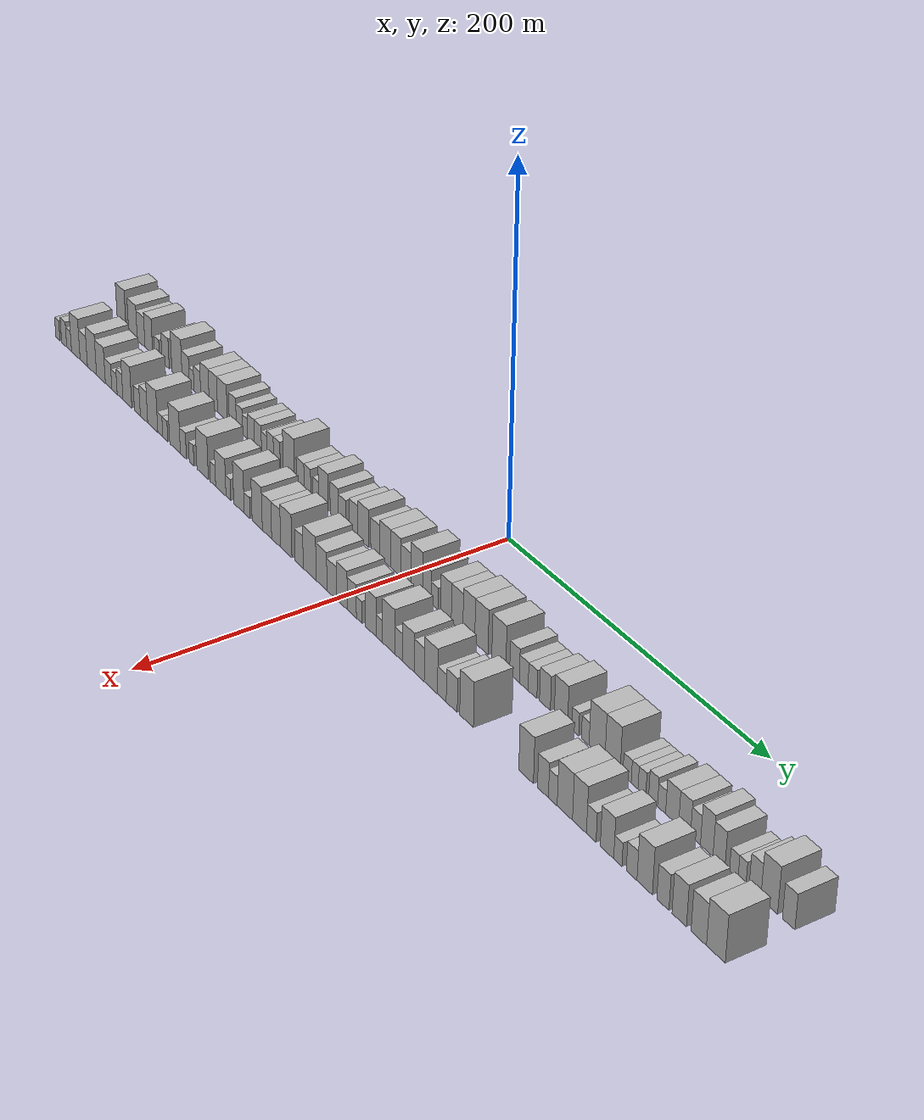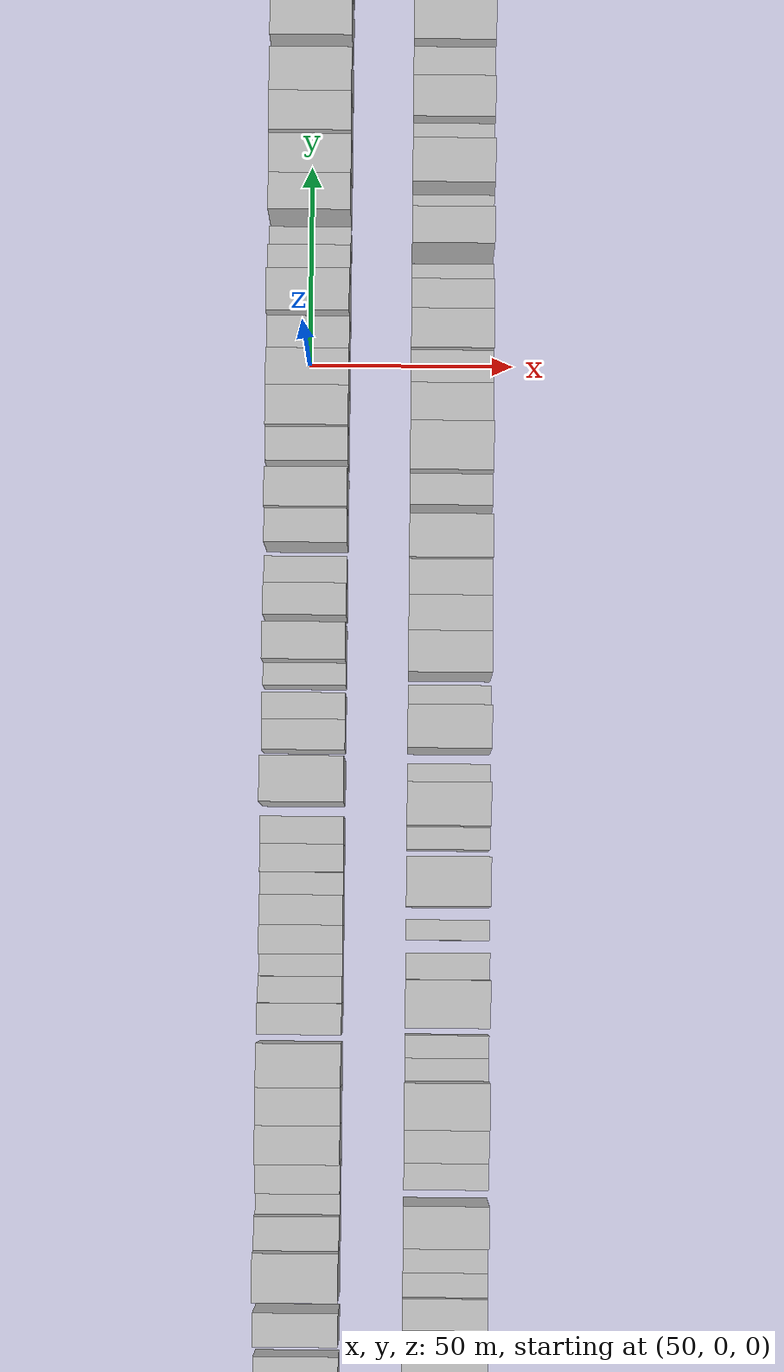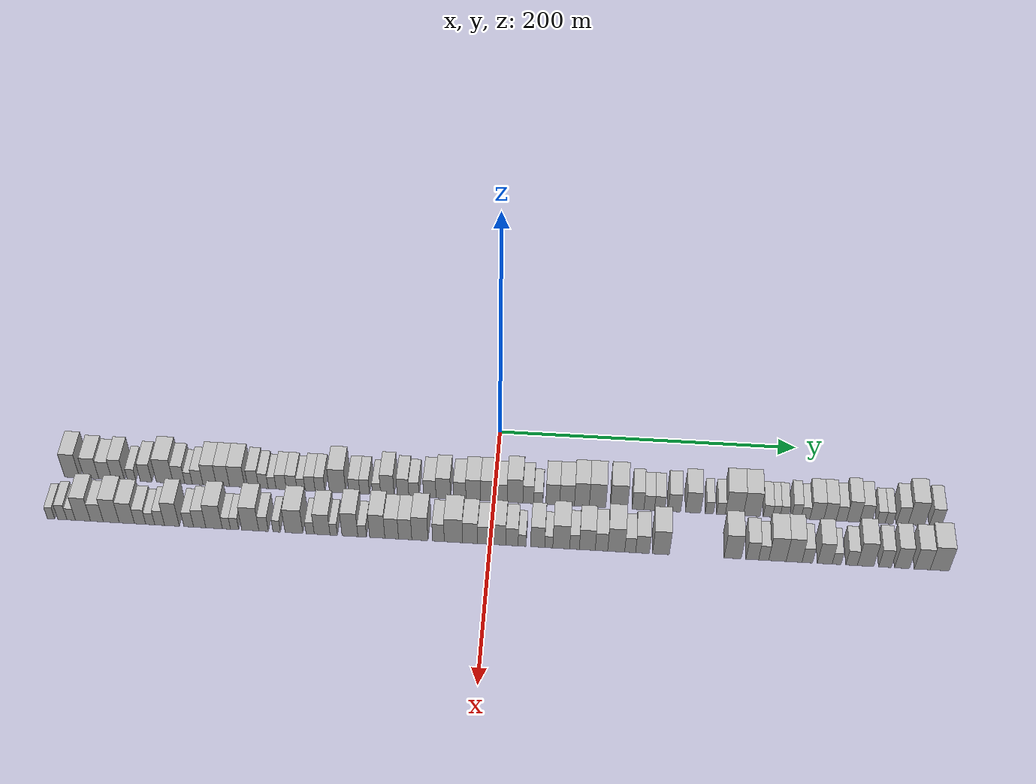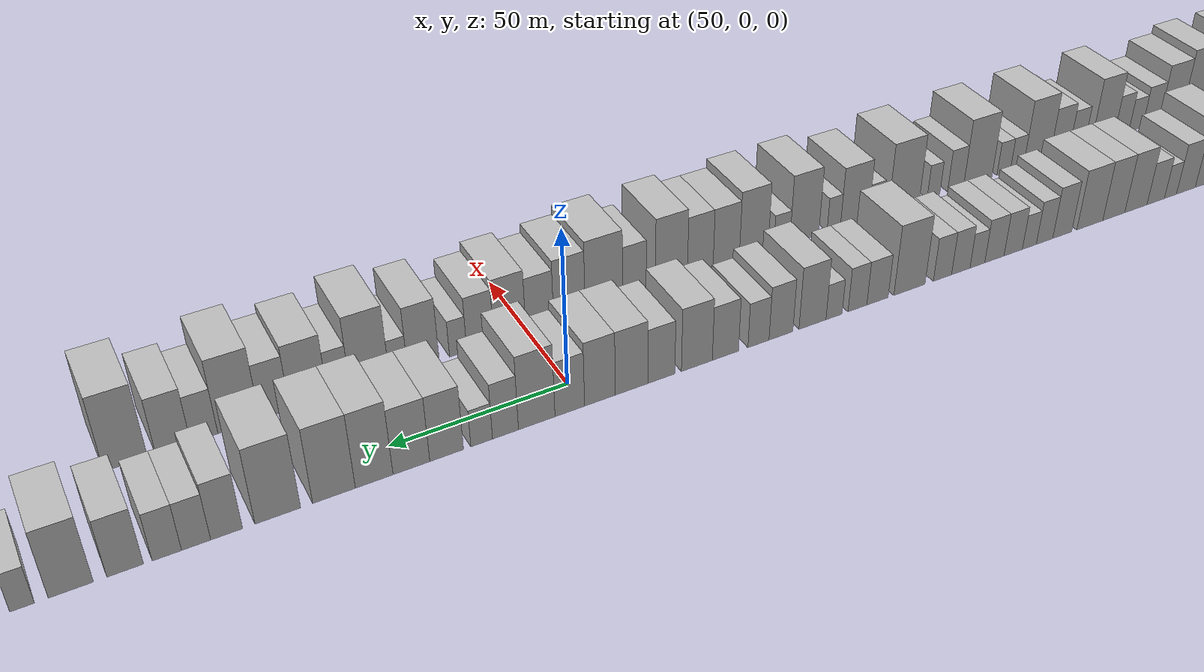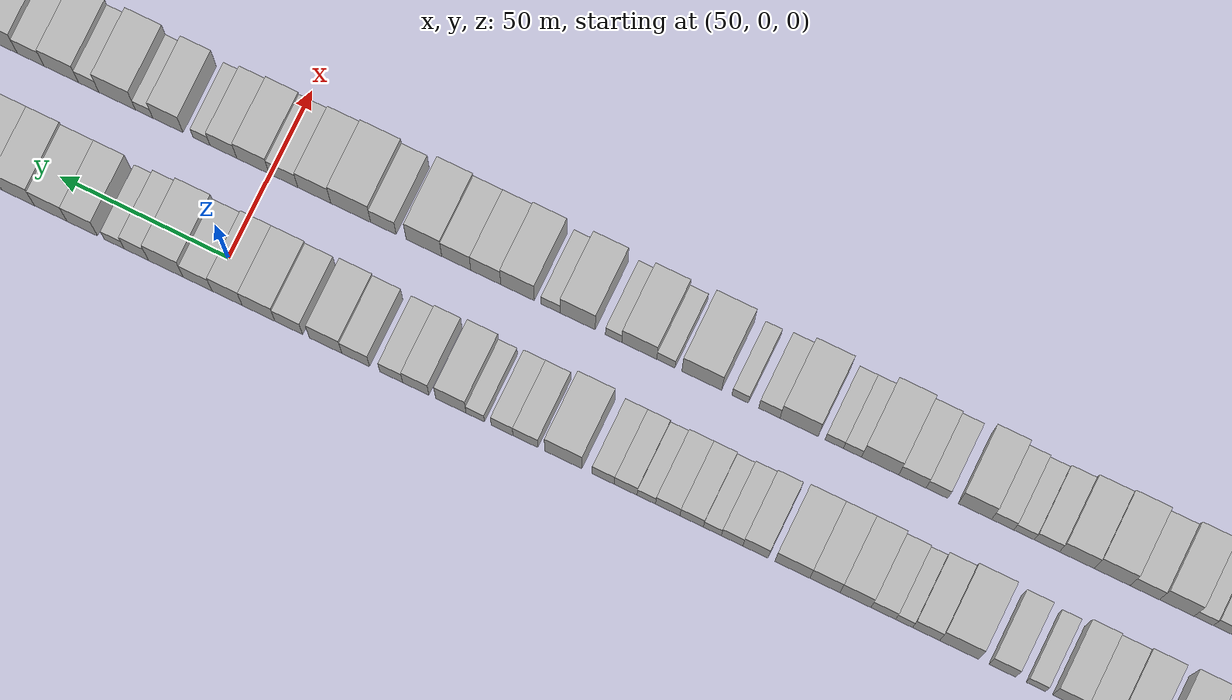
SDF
<sdf version="1.6">
 <world name="default">
  <scene>
   <sky><clouds><speed>12</speed></clouds></sky>
   <ambient>0.4 0.4 0.4 1</ambient>
   <background>0.7 0.7 0.7 1</background>
   <shadows>1</shadows>
  </scene>
  <gravity>0 0 -9.8066</gravity>
  <magnetic_field>6e-06 2.3e-05 -4.2e-05</magnetic_field>
  <physics default="0" name="default_physics" type="ode">
   <ode>
    <solver>
     <type>quick</type>
     <iters>10</iters>
     <sor>1.0</sor>
     <use_dynamic_moi_rescaling>0</use_dynamic_moi_rescaling>
    </solver>
    <constraints>
     <cfm>0</cfm>
     <erp>0.2</erp>
     <contact_max_correcting_vel>100</contact_max_correcting_vel>
     <contact_surface_layer>0.001</contact_surface_layer>
    </constraints>
   </ode>
   <max_step_size>0.004</max_step_size>
   <real_time_factor>1</real_time_factor>
   <real_time_update_rate>250</real_time_update_rate>
  </physics>
  <light name="sun" type="directional">
   <pose>0 0 10 0 0 0</pose>
   <diffuse>0.8 0.8 0.8 1</diffuse>
   <specular>0.2 0.2 0.2 1</specular>
   <attenuation>
    <range>1000</range>
    <constant>0.9</constant>
    <linear>0.01</linear>
    <quadratic>0.001</quadratic>
   </attenuation>
   <direction>-0.5 0.1 -0.9</direction>
  </light>
  <model name="building_1">
   <static>1</static>
   <pose>50.0000 -281.9514 0 0.000000 0.000000 0.000000</pose>
   <link name="link">
    <pose>0 0 12.00 0 0 0</pose>
    <collision name="collision"><geometry><box><size>20.0000 10.0973 24.0000</size></box></geometry></collision>
    <visual name="visual">
     <cast_shadows>0</cast_shadows>
     <geometry><box><size>20.0000 10.0973 24.0000</size></box></geometry>
     <material>
      <script>
       <uri>model://HANNAS_wall/materials/scripts</uri>
       <uri>model://HANNAS_wall/materials/textures</uri>
       <name>vrc/HANNAS_wall</name>
      </script>
     </material>
    </visual>
   </link>
  </model>
  <model name="building_2">
   <static>1</static>
   <pose>50.0000 -268.9650 0 0.000000 0.000000 0.000000</pose>
   <link name="link">
    <pose>0 0 10.50 0 0 0</pose>
    <collision name="collision"><geometry><box><size>20.0000 9.8755 21.0000</size></box></geometry></collision>
    <visual name="visual">
     <cast_shadows>0</cast_shadows>
     <geometry><box><size>20.0000 9.8755 21.0000</size></box></geometry>
     <material>
      <script>
       <uri>model://HANNAS_wall/materials/scripts</uri>
       <uri>model://HANNAS_wall/materials/textures</uri>
       <name>vrc/HANNAS_wall</name>
      </script>
     </material>
    </visual>
   </link>
  </model>
  <model name="building_3">
   <static>1</static>
   <pose>50.0000 -259.6310 0 0.000000 0.000000 0.000000</pose>
   <link name="link">
    <pose>0 0 9.00 0 0 0</pose>
    <collision name="collision"><geometry><box><size>20.0000 8.7925 18.0000</size></box></geometry></collision>
    <visual name="visual">
     <cast_shadows>0</cast_shadows>
     <geometry><box><size>20.0000 8.7925 18.0000</size></box></geometry>
     <material>
      <script>
       <uri>model://HANNAS_wall/materials/scripts</uri>
       <uri>model://HANNAS_wall/materials/textures</uri>
       <name>vrc/HANNAS_wall</name>
      </script>
     </material>
    </visual>
   </link>
  </model>
  <model name="building_4">
   <static>1</static>
   <pose>50.0000 -250.9372 0 0.000000 0.000000 0.000000</pose>
   <link name="link">
    <pose>0 0 10.50 0 0 0</pose>
    <collision name="collision"><geometry><box><size>20.0000 8.5951 21.0000</size></box></geometry></collision>
    <visual name="visual">
     <cast_shadows>0</cast_shadows>
     <geometry><box><size>20.0000 8.5951 21.0000</size></box></geometry>
     <material>
      <script>
       <uri>model://HANNAS_wall/materials/scripts</uri>
       <uri>model://HANNAS_wall/materials/textures</uri>
       <name>vrc/HANNAS_wall</name>
      </script>
     </material>
    </visual>
   </link>
  </model>
  <model name="building_5">
   <static>1</static>
   <pose>50.0000 -241.8137 0 0.000000 0.000000 0.000000</pose>
   <link name="link">
    <pose>0 0 6.00 0 0 0</pose>
    <collision name="collision"><geometry><box><size>20.0000 5.6519 12.0000</size></box></geometry></collision>
    <visual name="visual">
     <cast_shadows>0</cast_shadows>
     <geometry><box><size>20.0000 5.6519 12.0000</size></box></geometry>
     <material>
      <script>
       <uri>model://HANNAS_wall/materials/scripts</uri>
       <uri>model://HANNAS_wall/materials/textures</uri>
       <name>vrc/HANNAS_wall</name>
      </script>
     </material>
    </visual>
   </link>
  </model>
  <model name="building_6">
   <static>1</static>
   <pose>50.0000 -232.0887 0 0.000000 0.000000 0.000000</pose>
   <link name="link">
    <pose>0 0 9.00 0 0 0</pose>
    <collision name="collision"><geometry><box><size>20.0000 7.7981 18.0000</size></box></geometry></collision>
    <visual name="visual">
     <cast_shadows>0</cast_shadows>
     <geometry><box><size>20.0000 7.7981 18.0000</size></box></geometry>
     <material>
      <script>
       <uri>model://HANNAS_wall/materials/scripts</uri>
       <uri>model://HANNAS_wall/materials/textures</uri>
       <name>vrc/HANNAS_wall</name>
      </script>
     </material>
    </visual>
   </link>
  </model>
  <model name="building_7">
   <static>1</static>
   <pose>50.0000 -219.5472 0 0.000000 0.000000 0.000000</pose>
   <link name="link">
    <pose>0 0 12.00 0 0 0</pose>
    <collision name="collision"><geometry><box><size>20.0000 11.2847 24.0000</size></box></geometry></collision>
    <visual name="visual">
     <cast_shadows>0</cast_shadows>
     <geometry><box><size>20.0000 11.2847 24.0000</size></box></geometry>
     <material>
      <script>
       <uri>model://HANNAS_wall/materials/scripts</uri>
       <uri>model://HANNAS_wall/materials/textures</uri>
       <name>vrc/HANNAS_wall</name>
      </script>
     </material>
    </visual>
   </link>
  </model>
  <model name="building_8">
   <static>1</static>
   <pose>50.0000 -209.9635 0 0.000000 0.000000 0.000000</pose>
   <link name="link">
    <pose>0 0 9.00 0 0 0</pose>
    <collision name="collision"><geometry><box><size>20.0000 7.8828 18.0000</size></box></geometry></collision>
    <visual name="visual">
     <cast_shadows>0</cast_shadows>
     <geometry><box><size>20.0000 7.8828 18.0000</size></box></geometry>
     <material>
      <script>
       <uri>model://HANNAS_wall/materials/scripts</uri>
       <uri>model://HANNAS_wall/materials/textures</uri>
       <name>vrc/HANNAS_wall</name>
      </script>
     </material>
    </visual>
   </link>
  </model>
  <model name="building_9">
   <static>1</static>
   <pose>50.0000 -203.5387 0 0.000000 0.000000 0.000000</pose>
   <link name="link">
    <pose>0 0 6.00 0 0 0</pose>
    <collision name="collision"><geometry><box><size>20.0000 4.9668 12.0000</size></box></geometry></collision>
    <visual name="visual">
     <cast_shadows>0</cast_shadows>
     <geometry><box><size>20.0000 4.9668 12.0000</size></box></geometry>
     <material>
      <script>
       <uri>model://HANNAS_wall/materials/scripts</uri>
       <uri>model://HANNAS_wall/materials/textures</uri>
       <name>vrc/HANNAS_wall</name>
      </script>
     </material>
    </visual>
   </link>
  </model>
  <model name="building_10">
   <static>1</static>
   <pose>50.0000 -197.4601 0 0.000000 0.000000 0.000000</pose>
   <link name="link">
    <pose>0 0 7.50 0 0 0</pose>
    <collision name="collision"><geometry><box><size>20.0000 7.1904 15.0000</size></box></geometry></collision>
    <visual name="visual">
     <cast_shadows>0</cast_shadows>
     <geometry><box><size>20.0000 7.1904 15.0000</size></box></geometry>
     <material>
      <script>
       <uri>model://HANNAS_wall/materials/scripts</uri>
       <uri>model://HANNAS_wall/materials/textures</uri>
       <name>vrc/HANNAS_wall</name>
      </script>
     </material>
    </visual>
   </link>
  </model>
  <model name="building_11">
   <static>1</static>
   <pose>50.0000 -189.3527 0 0.000000 0.000000 0.000000</pose>
   <link name="link">
    <pose>0 0 10.50 0 0 0</pose>
    <collision name="collision"><geometry><box><size>20.0000 9.0244 21.0000</size></box></geometry></collision>
    <visual name="visual">
     <cast_shadows>0</cast_shadows>
     <geometry><box><size>20.0000 9.0244 21.0000</size></box></geometry>
     <material>
      <script>
       <uri>model://HANNAS_wall/materials/scripts</uri>
       <uri>model://HANNAS_wall/materials/textures</uri>
       <name>vrc/HANNAS_wall</name>
      </script>
     </material>
    </visual>
   </link>
  </model>
  <model name="building_12">
   <static>1</static>
   <pose>50.0000 -180.4518 0 0.000000 0.000000 0.000000</pose>
   <link name="link">
    <pose>0 0 10.50 0 0 0</pose>
    <collision name="collision"><geometry><box><size>20.0000 8.7775 21.0000</size></box></geometry></collision>
    <visual name="visual">
     <cast_shadows>0</cast_shadows>
     <geometry><box><size>20.0000 8.7775 21.0000</size></box></geometry>
     <material>
      <script>
       <uri>model://HANNAS_wall/materials/scripts</uri>
       <uri>model://HANNAS_wall/materials/textures</uri>
       <name>vrc/HANNAS_wall</name>
      </script>
     </material>
    </visual>
   </link>
  </model>
  <model name="building_13">
   <static>1</static>
   <pose>50.0000 -170.9487 0 0.000000 0.000000 0.000000</pose>
   <link name="link">
    <pose>0 0 10.50 0 0 0</pose>
    <collision name="collision"><geometry><box><size>20.0000 10.2286 21.0000</size></box></geometry></collision>
    <visual name="visual">
     <cast_shadows>0</cast_shadows>
     <geometry><box><size>20.0000 10.2286 21.0000</size></box></geometry>
     <material>
      <script>
       <uri>model://HANNAS_wall/materials/scripts</uri>
       <uri>model://HANNAS_wall/materials/textures</uri>
       <name>vrc/HANNAS_wall</name>
      </script>
     </material>
    </visual>
   </link>
  </model>
  <model name="building_14">
   <static>1</static>
   <pose>50.0000 -160.1610 0 0.000000 0.000000 0.000000</pose>
   <link name="link">
    <pose>0 0 9.00 0 0 0</pose>
    <collision name="collision"><geometry><box><size>20.0000 7.3468 18.0000</size></box></geometry></collision>
    <visual name="visual">
     <cast_shadows>0</cast_shadows>
     <geometry><box><size>20.0000 7.3468 18.0000</size></box></geometry>
     <material>
      <script>
       <uri>model://HANNAS_wall/materials/scripts</uri>
       <uri>model://HANNAS_wall/materials/textures</uri>
       <name>vrc/HANNAS_wall</name>
      </script>
     </material>
    </visual>
   </link>
  </model>
  <model name="building_15">
   <static>1</static>
   <pose>50.0000 -153.3467 0 0.000000 0.000000 0.000000</pose>
   <link name="link">
    <pose>0 0 7.50 0 0 0</pose>
    <collision name="collision"><geometry><box><size>20.0000 6.2819 15.0000</size></box></geometry></collision>
    <visual name="visual">
     <cast_shadows>0</cast_shadows>
     <geometry><box><size>20.0000 6.2819 15.0000</size></box></geometry>
     <material>
      <script>
       <uri>model://HANNAS_wall/materials/scripts</uri>
       <uri>model://HANNAS_wall/materials/textures</uri>
       <name>vrc/HANNAS_wall</name>
      </script>
     </material>
    </visual>
   </link>
  </model>
  <model name="building_16">
   <static>1</static>
   <pose>50.0000 -147.5695 0 0.000000 0.000000 0.000000</pose>
   <link name="link">
    <pose>0 0 6.00 0 0 0</pose>
    <collision name="collision"><geometry><box><size>20.0000 5.2724 12.0000</size></box></geometry></collision>
    <visual name="visual">
     <cast_shadows>0</cast_shadows>
     <geometry><box><size>20.0000 5.2724 12.0000</size></box></geometry>
     <material>
      <script>
       <uri>model://HANNAS_wall/materials/scripts</uri>
       <uri>model://HANNAS_wall/materials/textures</uri>
       <name>vrc/HANNAS_wall</name>
      </script>
     </material>
    </visual>
   </link>
  </model>
  <model name="building_17">
   <static>1</static>
   <pose>50.0000 -141.4911 0 0.000000 0.000000 0.000000</pose>
   <link name="link">
    <pose>0 0 7.50 0 0 0</pose>
    <collision name="collision"><geometry><box><size>20.0000 6.8844 15.0000</size></box></geometry></collision>
    <visual name="visual">
     <cast_shadows>0</cast_shadows>
     <geometry><box><size>20.0000 6.8844 15.0000</size></box></geometry>
     <material>
      <script>
       <uri>model://HANNAS_wall/materials/scripts</uri>
       <uri>model://HANNAS_wall/materials/textures</uri>
       <name>vrc/HANNAS_wall</name>
      </script>
     </material>
    </visual>
   </link>
  </model>
  <model name="building_18">
   <static>1</static>
   <pose>50.0000 -134.4812 0 0.000000 0.000000 0.000000</pose>
   <link name="link">
    <pose>0 0 7.50 0 0 0</pose>
    <collision name="collision"><geometry><box><size>20.0000 7.1355 15.0000</size></box></geometry></collision>
    <visual name="visual">
     <cast_shadows>0</cast_shadows>
     <geometry><box><size>20.0000 7.1355 15.0000</size></box></geometry>
     <material>
      <script>
       <uri>model://HANNAS_wall/materials/scripts</uri>
       <uri>model://HANNAS_wall/materials/textures</uri>
       <name>vrc/HANNAS_wall</name>
      </script>
     </material>
    </visual>
   </link>
  </model>
  <model name="building_19">
   <static>1</static>
   <pose>50.0000 -128.2064 0 0.000000 0.000000 0.000000</pose>
   <link name="link">
    <pose>0 0 6.00 0 0 0</pose>
    <collision name="collision"><geometry><box><size>20.0000 5.4142 12.0000</size></box></geometry></collision>
    <visual name="visual">
     <cast_shadows>0</cast_shadows>
     <geometry><box><size>20.0000 5.4142 12.0000</size></box></geometry>
     <material>
      <script>
       <uri>model://HANNAS_wall/materials/scripts</uri>
       <uri>model://HANNAS_wall/materials/textures</uri>
       <name>vrc/HANNAS_wall</name>
      </script>
     </material>
    </visual>
   </link>
  </model>
  <model name="building_20">
   <static>1</static>
   <pose>50.0000 -122.1646 0 0.000000 0.000000 0.000000</pose>
   <link name="link">
    <pose>0 0 7.50 0 0 0</pose>
    <collision name="collision"><geometry><box><size>20.0000 6.6693 15.0000</size></box></geometry></collision>
    <visual name="visual">
     <cast_shadows>0</cast_shadows>
     <geometry><box><size>20.0000 6.6693 15.0000</size></box></geometry>
     <material>
      <script>
       <uri>model://HANNAS_wall/materials/scripts</uri>
       <uri>model://HANNAS_wall/materials/textures</uri>
       <name>vrc/HANNAS_wall</name>
      </script>
     </material>
    </visual>
   </link>
  </model>
  <model name="building_21">
   <static>1</static>
   <pose>50.0000 -115.5677 0 0.000000 0.000000 0.000000</pose>
   <link name="link">
    <pose>0 0 7.50 0 0 0</pose>
    <collision name="collision"><geometry><box><size>20.0000 6.5244 15.0000</size></box></geometry></collision>
    <visual name="visual">
     <cast_shadows>0</cast_shadows>
     <geometry><box><size>20.0000 6.5244 15.0000</size></box></geometry>
     <material>
      <script>
       <uri>model://HANNAS_wall/materials/scripts</uri>
       <uri>model://HANNAS_wall/materials/textures</uri>
       <name>vrc/HANNAS_wall</name>
      </script>
     </material>
    </visual>
   </link>
  </model>
  <model name="building_22">
   <static>1</static>
   <pose>50.0000 -103.8464 0 0.000000 0.000000 0.000000</pose>
   <link name="link">
    <pose>0 0 12.00 0 0 0</pose>
    <collision name="collision"><geometry><box><size>20.0000 10.9184 24.0000</size></box></geometry></collision>
    <visual name="visual">
     <cast_shadows>0</cast_shadows>
     <geometry><box><size>20.0000 10.9184 24.0000</size></box></geometry>
     <material>
      <script>
       <uri>model://HANNAS_wall/materials/scripts</uri>
       <uri>model://HANNAS_wall/materials/textures</uri>
       <name>vrc/HANNAS_wall</name>
      </script>
     </material>
    </visual>
   </link>
  </model>
  <model name="building_23">
   <static>1</static>
   <pose>50.0000 -92.7179 0 0.000000 0.000000 0.000000</pose>
   <link name="link">
    <pose>0 0 7.50 0 0 0</pose>
    <collision name="collision"><geometry><box><size>20.0000 7.3385 15.0000</size></box></geometry></collision>
    <visual name="visual">
     <cast_shadows>0</cast_shadows>
     <geometry><box><size>20.0000 7.3385 15.0000</size></box></geometry>
     <material>
      <script>
       <uri>model://HANNAS_wall/materials/scripts</uri>
       <uri>model://HANNAS_wall/materials/textures</uri>
       <name>vrc/HANNAS_wall</name>
      </script>
     </material>
    </visual>
   </link>
  </model>
  <model name="building_24">
   <static>1</static>
   <pose>50.0000 -85.8513 0 0.000000 0.000000 0.000000</pose>
   <link name="link">
    <pose>0 0 7.50 0 0 0</pose>
    <collision name="collision"><geometry><box><size>20.0000 6.3947 15.0000</size></box></geometry></collision>
    <visual name="visual">
     <cast_shadows>0</cast_shadows>
     <geometry><box><size>20.0000 6.3947 15.0000</size></box></geometry>
     <material>
      <script>
       <uri>model://HANNAS_wall/materials/scripts</uri>
       <uri>model://HANNAS_wall/materials/textures</uri>
       <name>vrc/HANNAS_wall</name>
      </script>
     </material>
    </visual>
   </link>
  </model>
  <model name="building_25">
   <static>1</static>
   <pose>50.0000 -77.9484 0 0.000000 0.000000 0.000000</pose>
   <link name="link">
    <pose>0 0 6.00 0 0 0</pose>
    <collision name="collision"><geometry><box><size>20.0000 5.4112 12.0000</size></box></geometry></collision>
    <visual name="visual">
     <cast_shadows>0</cast_shadows>
     <geometry><box><size>20.0000 5.4112 12.0000</size></box></geometry>
     <material>
      <script>
       <uri>model://HANNAS_wall/materials/scripts</uri>
       <uri>model://HANNAS_wall/materials/textures</uri>
       <name>vrc/HANNAS_wall</name>
      </script>
     </material>
    </visual>
   </link>
  </model>
  <model name="building_26">
   <static>1</static>
   <pose>50.0000 -70.7677 0 0.000000 0.000000 0.000000</pose>
   <link name="link">
    <pose>0 0 10.50 0 0 0</pose>
    <collision name="collision"><geometry><box><size>20.0000 8.9503 21.0000</size></box></geometry></collision>
    <visual name="visual">
     <cast_shadows>0</cast_shadows>
     <geometry><box><size>20.0000 8.9503 21.0000</size></box></geometry>
     <material>
      <script>
       <uri>model://HANNAS_wall/materials/scripts</uri>
       <uri>model://HANNAS_wall/materials/textures</uri>
       <name>vrc/HANNAS_wall</name>
      </script>
     </material>
    </visual>
   </link>
  </model>
  <model name="building_27">
   <static>1</static>
   <pose>50.0000 -60.4169 0 0.000000 0.000000 0.000000</pose>
   <link name="link">
    <pose>0 0 9.00 0 0 0</pose>
    <collision name="collision"><geometry><box><size>20.0000 7.7512 18.0000</size></box></geometry></collision>
    <visual name="visual">
     <cast_shadows>0</cast_shadows>
     <geometry><box><size>20.0000 7.7512 18.0000</size></box></geometry>
     <material>
      <script>
       <uri>model://HANNAS_wall/materials/scripts</uri>
       <uri>model://HANNAS_wall/materials/textures</uri>
       <name>vrc/HANNAS_wall</name>
      </script>
     </material>
    </visual>
   </link>
  </model>
  <model name="building_28">
   <static>1</static>
   <pose>50.0000 -53.1641 0 0.000000 0.000000 0.000000</pose>
   <link name="link">
    <pose>0 0 7.50 0 0 0</pose>
    <collision name="collision"><geometry><box><size>20.0000 6.7545 15.0000</size></box></geometry></collision>
    <visual name="visual">
     <cast_shadows>0</cast_shadows>
     <geometry><box><size>20.0000 6.7545 15.0000</size></box></geometry>
     <material>
      <script>
       <uri>model://HANNAS_wall/materials/scripts</uri>
       <uri>model://HANNAS_wall/materials/textures</uri>
       <name>vrc/HANNAS_wall</name>
      </script>
     </material>
    </visual>
   </link>
  </model>
  <model name="building_29">
   <static>1</static>
   <pose>50.0000 -42.6650 0 0.000000 0.000000 0.000000</pose>
   <link name="link">
    <pose>0 0 9.00 0 0 0</pose>
    <collision name="collision"><geometry><box><size>20.0000 8.2437 18.0000</size></box></geometry></collision>
    <visual name="visual">
     <cast_shadows>0</cast_shadows>
     <geometry><box><size>20.0000 8.2437 18.0000</size></box></geometry>
     <material>
      <script>
       <uri>model://HANNAS_wall/materials/scripts</uri>
       <uri>model://HANNAS_wall/materials/textures</uri>
       <name>vrc/HANNAS_wall</name>
      </script>
     </material>
    </visual>
   </link>
  </model>
  <model name="building_30">
   <static>1</static>
   <pose>50.0000 -33.7552 0 0.000000 0.000000 0.000000</pose>
   <link name="link">
    <pose>0 0 10.50 0 0 0</pose>
    <collision name="collision"><geometry><box><size>20.0000 9.5758 21.0000</size></box></geometry></collision>
    <visual name="visual">
     <cast_shadows>0</cast_shadows>
     <geometry><box><size>20.0000 9.5758 21.0000</size></box></geometry>
     <material>
      <script>
       <uri>model://HANNAS_wall/materials/scripts</uri>
       <uri>model://HANNAS_wall/materials/textures</uri>
       <name>vrc/HANNAS_wall</name>
      </script>
     </material>
    </visual>
   </link>
  </model>
  <model name="building_31">
   <static>1</static>
   <pose>50.0000 -22.8692 0 0.000000 0.000000 0.000000</pose>
   <link name="link">
    <pose>0 0 9.00 0 0 0</pose>
    <collision name="collision"><geometry><box><size>20.0000 8.1962 18.0000</size></box></geometry></collision>
    <visual name="visual">
     <cast_shadows>0</cast_shadows>
     <geometry><box><size>20.0000 8.1962 18.0000</size></box></geometry>
     <material>
      <script>
       <uri>model://HANNAS_wall/materials/scripts</uri>
       <uri>model://HANNAS_wall/materials/textures</uri>
       <name>vrc/HANNAS_wall</name>
      </script>
     </material>
    </visual>
   </link>
  </model>
  <model name="building_32">
   <static>1</static>
   <pose>50.0000 -13.9225 0 0.000000 0.000000 0.000000</pose>
   <link name="link">
    <pose>0 0 10.50 0 0 0</pose>
    <collision name="collision"><geometry><box><size>20.0000 9.6973 21.0000</size></box></geometry></collision>
    <visual name="visual">
     <cast_shadows>0</cast_shadows>
     <geometry><box><size>20.0000 9.6973 21.0000</size></box></geometry>
     <material>
      <script>
       <uri>model://HANNAS_wall/materials/scripts</uri>
       <uri>model://HANNAS_wall/materials/textures</uri>
       <name>vrc/HANNAS_wall</name>
      </script>
     </material>
    </visual>
   </link>
  </model>
  <model name="building_33">
   <static>1</static>
   <pose>50.0000 -4.5877 0 0.000000 0.000000 0.000000</pose>
   <link name="link">
    <pose>0 0 10.50 0 0 0</pose>
    <collision name="collision"><geometry><box><size>20.0000 8.9723 21.0000</size></box></geometry></collision>
    <visual name="visual">
     <cast_shadows>0</cast_shadows>
     <geometry><box><size>20.0000 8.9723 21.0000</size></box></geometry>
     <material>
      <script>
       <uri>model://HANNAS_wall/materials/scripts</uri>
       <uri>model://HANNAS_wall/materials/textures</uri>
       <name>vrc/HANNAS_wall</name>
      </script>
     </material>
    </visual>
   </link>
  </model>
  <model name="building_34">
   <static>1</static>
   <pose>50.0000 4.1626 0 0.000000 0.000000 0.000000</pose>
   <link name="link">
    <pose>0 0 9.00 0 0 0</pose>
    <collision name="collision"><geometry><box><size>20.0000 8.5283 18.0000</size></box></geometry></collision>
    <visual name="visual">
     <cast_shadows>0</cast_shadows>
     <geometry><box><size>20.0000 8.5283 18.0000</size></box></geometry>
     <material>
      <script>
       <uri>model://HANNAS_wall/materials/scripts</uri>
       <uri>model://HANNAS_wall/materials/textures</uri>
       <name>vrc/HANNAS_wall</name>
      </script>
     </material>
    </visual>
   </link>
  </model>
  <model name="building_35">
   <static>1</static>
   <pose>50.0000 13.5947 0 0.000000 0.000000 0.000000</pose>
   <link name="link">
    <pose>0 0 12.00 0 0 0</pose>
    <collision name="collision"><geometry><box><size>20.0000 10.3360 24.0000</size></box></geometry></collision>
    <visual name="visual">
     <cast_shadows>0</cast_shadows>
     <geometry><box><size>20.0000 10.3360 24.0000</size></box></geometry>
     <material>
      <script>
       <uri>model://HANNAS_wall/materials/scripts</uri>
       <uri>model://HANNAS_wall/materials/textures</uri>
       <name>vrc/HANNAS_wall</name>
      </script>
     </material>
    </visual>
   </link>
  </model>
  <model name="building_36">
   <static>1</static>
   <pose>50.0000 22.3643 0 0.000000 0.000000 0.000000</pose>
   <link name="link">
    <pose>0 0 9.00 0 0 0</pose>
    <collision name="collision"><geometry><box><size>20.0000 7.2032 18.0000</size></box></geometry></collision>
    <visual name="visual">
     <cast_shadows>0</cast_shadows>
     <geometry><box><size>20.0000 7.2032 18.0000</size></box></geometry>
     <material>
      <script>
       <uri>model://HANNAS_wall/materials/scripts</uri>
       <uri>model://HANNAS_wall/materials/textures</uri>
       <name>vrc/HANNAS_wall</name>
      </script>
     </material>
    </visual>
   </link>
  </model>
  <model name="building_37">
   <static>1</static>
   <pose>50.0000 28.9423 0 0.000000 0.000000 0.000000</pose>
   <link name="link">
    <pose>0 0 6.00 0 0 0</pose>
    <collision name="collision"><geometry><box><size>20.0000 5.9528 12.0000</size></box></geometry></collision>
    <visual name="visual">
     <cast_shadows>0</cast_shadows>
     <geometry><box><size>20.0000 5.9528 12.0000</size></box></geometry>
     <material>
      <script>
       <uri>model://HANNAS_wall/materials/scripts</uri>
       <uri>model://HANNAS_wall/materials/textures</uri>
       <name>vrc/HANNAS_wall</name>
      </script>
     </material>
    </visual>
   </link>
  </model>
  <model name="building_38">
   <static>1</static>
   <pose>50.0000 38.4510 0 0.000000 0.000000 0.000000</pose>
   <link name="link">
    <pose>0 0 10.50 0 0 0</pose>
    <collision name="collision"><geometry><box><size>20.0000 9.0646 21.0000</size></box></geometry></collision>
    <visual name="visual">
     <cast_shadows>0</cast_shadows>
     <geometry><box><size>20.0000 9.0646 21.0000</size></box></geometry>
     <material>
      <script>
       <uri>model://HANNAS_wall/materials/scripts</uri>
       <uri>model://HANNAS_wall/materials/textures</uri>
       <name>vrc/HANNAS_wall</name>
      </script>
     </material>
    </visual>
   </link>
  </model>
  <model name="building_39">
   <static>1</static>
   <pose>50.0000 47.8418 0 0.000000 0.000000 0.000000</pose>
   <link name="link">
    <pose>0 0 10.50 0 0 0</pose>
    <collision name="collision"><geometry><box><size>20.0000 9.7169 21.0000</size></box></geometry></collision>
    <visual name="visual">
     <cast_shadows>0</cast_shadows>
     <geometry><box><size>20.0000 9.7169 21.0000</size></box></geometry>
     <material>
      <script>
       <uri>model://HANNAS_wall/materials/scripts</uri>
       <uri>model://HANNAS_wall/materials/textures</uri>
       <name>vrc/HANNAS_wall</name>
      </script>
     </material>
    </visual>
   </link>
  </model>
  <model name="building_40">
   <static>1</static>
   <pose>50.0000 57.5797 0 0.000000 0.000000 0.000000</pose>
   <link name="link">
    <pose>0 0 12.00 0 0 0</pose>
    <collision name="collision"><geometry><box><size>20.0000 9.7589 24.0000</size></box></geometry></collision>
    <visual name="visual">
     <cast_shadows>0</cast_shadows>
     <geometry><box><size>20.0000 9.7589 24.0000</size></box></geometry>
     <material>
      <script>
       <uri>model://HANNAS_wall/materials/scripts</uri>
       <uri>model://HANNAS_wall/materials/textures</uri>
       <name>vrc/HANNAS_wall</name>
      </script>
     </material>
    </visual>
   </link>
  </model>
  <model name="building_41">
   <static>1</static>
   <pose>50.0000 67.8784 0 0.000000 0.000000 0.000000</pose>
   <link name="link">
    <pose>0 0 12.00 0 0 0</pose>
    <collision name="collision"><geometry><box><size>20.0000 10.8384 24.0000</size></box></geometry></collision>
    <visual name="visual">
     <cast_shadows>0</cast_shadows>
     <geometry><box><size>20.0000 10.8384 24.0000</size></box></geometry>
     <material>
      <script>
       <uri>model://HANNAS_wall/materials/scripts</uri>
       <uri>model://HANNAS_wall/materials/textures</uri>
       <name>vrc/HANNAS_wall</name>
      </script>
     </material>
    </visual>
   </link>
  </model>
  <model name="building_42">
   <static>1</static>
   <pose>50.0000 81.9233 0 0.000000 0.000000 0.000000</pose>
   <link name="link">
    <pose>0 0 12.00 0 0 0</pose>
    <collision name="collision"><geometry><box><size>20.0000 11.2516 24.0000</size></box></geometry></collision>
    <visual name="visual">
     <cast_shadows>0</cast_shadows>
     <geometry><box><size>20.0000 11.2516 24.0000</size></box></geometry>
     <material>
      <script>
       <uri>model://HANNAS_wall/materials/scripts</uri>
       <uri>model://HANNAS_wall/materials/textures</uri>
       <name>vrc/HANNAS_wall</name>
      </script>
     </material>
    </visual>
   </link>
  </model>
  <model name="building_43">
   <static>1</static>
   <pose>50.0000 94.3751 0 0.000000 0.000000 0.000000</pose>
   <link name="link">
    <pose>0 0 9.00 0 0 0</pose>
    <collision name="collision"><geometry><box><size>20.0000 7.6520 18.0000</size></box></geometry></collision>
    <visual name="visual">
     <cast_shadows>0</cast_shadows>
     <geometry><box><size>20.0000 7.6520 18.0000</size></box></geometry>
     <material>
      <script>
       <uri>model://HANNAS_wall/materials/scripts</uri>
       <uri>model://HANNAS_wall/materials/textures</uri>
       <name>vrc/HANNAS_wall</name>
      </script>
     </material>
    </visual>
   </link>
  </model>
  <model name="building_44">
   <static>1</static>
   <pose>50.0000 101.6487 0 0.000000 0.000000 0.000000</pose>
   <link name="link">
    <pose>0 0 7.50 0 0 0</pose>
    <collision name="collision"><geometry><box><size>20.0000 6.8953 15.0000</size></box></geometry></collision>
    <visual name="visual">
     <cast_shadows>0</cast_shadows>
     <geometry><box><size>20.0000 6.8953 15.0000</size></box></geometry>
     <material>
      <script>
       <uri>model://HANNAS_wall/materials/scripts</uri>
       <uri>model://HANNAS_wall/materials/textures</uri>
       <name>vrc/HANNAS_wall</name>
      </script>
     </material>
    </visual>
   </link>
  </model>
  <model name="building_45">
   <static>1</static>
   <pose>50.0000 108.5118 0 0.000000 0.000000 0.000000</pose>
   <link name="link">
    <pose>0 0 7.50 0 0 0</pose>
    <collision name="collision"><geometry><box><size>20.0000 6.8308 15.0000</size></box></geometry></collision>
    <visual name="visual">
     <cast_shadows>0</cast_shadows>
     <geometry><box><size>20.0000 6.8308 15.0000</size></box></geometry>
     <material>
      <script>
       <uri>model://HANNAS_wall/materials/scripts</uri>
       <uri>model://HANNAS_wall/materials/textures</uri>
       <name>vrc/HANNAS_wall</name>
      </script>
     </material>
    </visual>
   </link>
  </model>
  <model name="building_46">
   <static>1</static>
   <pose>50.0000 118.1153 0 0.000000 0.000000 0.000000</pose>
   <link name="link">
    <pose>0 0 9.00 0 0 0</pose>
    <collision name="collision"><geometry><box><size>20.0000 8.3763 18.0000</size></box></geometry></collision>
    <visual name="visual">
     <cast_shadows>0</cast_shadows>
     <geometry><box><size>20.0000 8.3763 18.0000</size></box></geometry>
     <material>
      <script>
       <uri>model://HANNAS_wall/materials/scripts</uri>
       <uri>model://HANNAS_wall/materials/textures</uri>
       <name>vrc/HANNAS_wall</name>
      </script>
     </material>
    </visual>
   </link>
  </model>
  <model name="building_47">
   <static>1</static>
   <pose>50.0000 130.3355 0 0.000000 0.000000 0.000000</pose>
   <link name="link">
    <pose>0 0 10.50 0 0 0</pose>
    <collision name="collision"><geometry><box><size>20.0000 10.0640 21.0000</size></box></geometry></collision>
    <visual name="visual">
     <cast_shadows>0</cast_shadows>
     <geometry><box><size>20.0000 10.0640 21.0000</size></box></geometry>
     <material>
      <script>
       <uri>model://HANNAS_wall/materials/scripts</uri>
       <uri>model://HANNAS_wall/materials/textures</uri>
       <name>vrc/HANNAS_wall</name>
      </script>
     </material>
    </visual>
   </link>
  </model>
  <model name="building_48">
   <static>1</static>
   <pose>50.0000 141.0523 0 0.000000 0.000000 0.000000</pose>
   <link name="link">
    <pose>0 0 6.00 0 0 0</pose>
    <collision name="collision"><geometry><box><size>20.0000 5.3695 12.0000</size></box></geometry></collision>
    <visual name="visual">
     <cast_shadows>0</cast_shadows>
     <geometry><box><size>20.0000 5.3695 12.0000</size></box></geometry>
     <material>
      <script>
       <uri>model://HANNAS_wall/materials/scripts</uri>
       <uri>model://HANNAS_wall/materials/textures</uri>
       <name>vrc/HANNAS_wall</name>
      </script>
     </material>
    </visual>
   </link>
  </model>
  <model name="building_49">
   <static>1</static>
   <pose>50.0000 148.5847 0 0.000000 0.000000 0.000000</pose>
   <link name="link">
    <pose>0 0 6.00 0 0 0</pose>
    <collision name="collision"><geometry><box><size>20.0000 5.6953 12.0000</size></box></geometry></collision>
    <visual name="visual">
     <cast_shadows>0</cast_shadows>
     <geometry><box><size>20.0000 5.6953 12.0000</size></box></geometry>
     <material>
      <script>
       <uri>model://HANNAS_wall/materials/scripts</uri>
       <uri>model://HANNAS_wall/materials/textures</uri>
       <name>vrc/HANNAS_wall</name>
      </script>
     </material>
    </visual>
   </link>
  </model>
  <model name="building_50">
   <static>1</static>
   <pose>50.0000 157.2870 0 0.000000 0.000000 0.000000</pose>
   <link name="link">
    <pose>0 0 12.00 0 0 0</pose>
    <collision name="collision"><geometry><box><size>20.0000 11.7093 24.0000</size></box></geometry></collision>
    <visual name="visual">
     <cast_shadows>0</cast_shadows>
     <geometry><box><size>20.0000 11.7093 24.0000</size></box></geometry>
     <material>
      <script>
       <uri>model://HANNAS_wall/materials/scripts</uri>
       <uri>model://HANNAS_wall/materials/textures</uri>
       <name>vrc/HANNAS_wall</name>
      </script>
     </material>
    </visual>
   </link>
  </model>
  <model name="building_51">
   <static>1</static>
   <pose>50.0000 168.6387 0 0.000000 0.000000 0.000000</pose>
   <link name="link">
    <pose>0 0 12.00 0 0 0</pose>
    <collision name="collision"><geometry><box><size>20.0000 10.9941 24.0000</size></box></geometry></collision>
    <visual name="visual">
     <cast_shadows>0</cast_shadows>
     <geometry><box><size>20.0000 10.9941 24.0000</size></box></geometry>
     <material>
      <script>
       <uri>model://HANNAS_wall/materials/scripts</uri>
       <uri>model://HANNAS_wall/materials/textures</uri>
       <name>vrc/HANNAS_wall</name>
      </script>
     </material>
    </visual>
   </link>
  </model>
  <model name="building_52">
   <static>1</static>
   <pose>50.0000 179.1250 0 0.000000 0.000000 0.000000</pose>
   <link name="link">
    <pose>0 0 6.00 0 0 0</pose>
    <collision name="collision"><geometry><box><size>20.0000 5.9785 12.0000</size></box></geometry></collision>
    <visual name="visual">
     <cast_shadows>0</cast_shadows>
     <geometry><box><size>20.0000 5.9785 12.0000</size></box></geometry>
     <material>
      <script>
       <uri>model://HANNAS_wall/materials/scripts</uri>
       <uri>model://HANNAS_wall/materials/textures</uri>
       <name>vrc/HANNAS_wall</name>
      </script>
     </material>
    </visual>
   </link>
  </model>
  <model name="building_53">
   <static>1</static>
   <pose>50.0000 184.5413 0 0.000000 0.000000 0.000000</pose>
   <link name="link">
    <pose>0 0 6.00 0 0 0</pose>
    <collision name="collision"><geometry><box><size>20.0000 4.8540 12.0000</size></box></geometry></collision>
    <visual name="visual">
     <cast_shadows>0</cast_shadows>
     <geometry><box><size>20.0000 4.8540 12.0000</size></box></geometry>
     <material>
      <script>
       <uri>model://HANNAS_wall/materials/scripts</uri>
       <uri>model://HANNAS_wall/materials/textures</uri>
       <name>vrc/HANNAS_wall</name>
      </script>
     </material>
    </visual>
   </link>
  </model>
  <model name="building_54">
   <static>1</static>
   <pose>50.0000 189.7033 0 0.000000 0.000000 0.000000</pose>
   <link name="link">
    <pose>0 0 6.00 0 0 0</pose>
    <collision name="collision"><geometry><box><size>20.0000 5.4699 12.0000</size></box></geometry></collision>
    <visual name="visual">
     <cast_shadows>0</cast_shadows>
     <geometry><box><size>20.0000 5.4699 12.0000</size></box></geometry>
     <material>
      <script>
       <uri>model://HANNAS_wall/materials/scripts</uri>
       <uri>model://HANNAS_wall/materials/textures</uri>
       <name>vrc/HANNAS_wall</name>
      </script>
     </material>
    </visual>
   </link>
  </model>
  <model name="building_55">
   <static>1</static>
   <pose>50.0000 197.5572 0 0.000000 0.000000 0.000000</pose>
   <link name="link">
    <pose>0 0 7.50 0 0 0</pose>
    <collision name="collision"><geometry><box><size>20.0000 6.2379 15.0000</size></box></geometry></collision>
    <visual name="visual">
     <cast_shadows>0</cast_shadows>
     <geometry><box><size>20.0000 6.2379 15.0000</size></box></geometry>
     <material>
      <script>
       <uri>model://HANNAS_wall/materials/scripts</uri>
       <uri>model://HANNAS_wall/materials/textures</uri>
       <name>vrc/HANNAS_wall</name>
      </script>
     </material>
    </visual>
   </link>
  </model>
  <model name="building_56">
   <static>1</static>
   <pose>50.0000 203.4955 0 0.000000 0.000000 0.000000</pose>
   <link name="link">
    <pose>0 0 6.00 0 0 0</pose>
    <collision name="collision"><geometry><box><size>20.0000 5.6386 12.0000</size></box></geometry></collision>
    <visual name="visual">
     <cast_shadows>0</cast_shadows>
     <geometry><box><size>20.0000 5.6386 12.0000</size></box></geometry>
     <material>
      <script>
       <uri>model://HANNAS_wall/materials/scripts</uri>
       <uri>model://HANNAS_wall/materials/textures</uri>
       <name>vrc/HANNAS_wall</name>
      </script>
     </material>
    </visual>
   </link>
  </model>
  <model name="building_57">
   <static>1</static>
   <pose>50.0000 210.8074 0 0.000000 0.000000 0.000000</pose>
   <link name="link">
    <pose>0 0 9.00 0 0 0</pose>
    <collision name="collision"><geometry><box><size>20.0000 8.9853 18.0000</size></box></geometry></collision>
    <visual name="visual">
     <cast_shadows>0</cast_shadows>
     <geometry><box><size>20.0000 8.9853 18.0000</size></box></geometry>
     <material>
      <script>
       <uri>model://HANNAS_wall/materials/scripts</uri>
       <uri>model://HANNAS_wall/materials/textures</uri>
       <name>vrc/HANNAS_wall</name>
      </script>
     </material>
    </visual>
   </link>
  </model>
  <model name="building_58">
   <static>1</static>
   <pose>50.0000 219.3591 0 0.000000 0.000000 0.000000</pose>
   <link name="link">
    <pose>0 0 9.00 0 0 0</pose>
    <collision name="collision"><geometry><box><size>20.0000 8.1181 18.0000</size></box></geometry></collision>
    <visual name="visual">
     <cast_shadows>0</cast_shadows>
     <geometry><box><size>20.0000 8.1181 18.0000</size></box></geometry>
     <material>
      <script>
       <uri>model://HANNAS_wall/materials/scripts</uri>
       <uri>model://HANNAS_wall/materials/textures</uri>
       <name>vrc/HANNAS_wall</name>
      </script>
     </material>
    </visual>
   </link>
  </model>
  <model name="building_59">
   <static>1</static>
   <pose>50.0000 226.7735 0 0.000000 0.000000 0.000000</pose>
   <link name="link">
    <pose>0 0 7.50 0 0 0</pose>
    <collision name="collision"><geometry><box><size>20.0000 6.7106 15.0000</size></box></geometry></collision>
    <visual name="visual">
     <cast_shadows>0</cast_shadows>
     <geometry><box><size>20.0000 6.7106 15.0000</size></box></geometry>
     <material>
      <script>
       <uri>model://HANNAS_wall/materials/scripts</uri>
       <uri>model://HANNAS_wall/materials/textures</uri>
       <name>vrc/HANNAS_wall</name>
      </script>
     </material>
    </visual>
   </link>
  </model>
  <model name="building_60">
   <static>1</static>
   <pose>50.0000 234.3361 0 0.000000 0.000000 0.000000</pose>
   <link name="link">
    <pose>0 0 10.50 0 0 0</pose>
    <collision name="collision"><geometry><box><size>20.0000 8.4145 21.0000</size></box></geometry></collision>
    <visual name="visual">
     <cast_shadows>0</cast_shadows>
     <geometry><box><size>20.0000 8.4145 21.0000</size></box></geometry>
     <material>
      <script>
       <uri>model://HANNAS_wall/materials/scripts</uri>
       <uri>model://HANNAS_wall/materials/textures</uri>
       <name>vrc/HANNAS_wall</name>
      </script>
     </material>
    </visual>
   </link>
  </model>
  <model name="building_61">
   <static>1</static>
   <pose>50.0000 242.5292 0 0.000000 0.000000 0.000000</pose>
   <link name="link">
    <pose>0 0 9.00 0 0 0</pose>
    <collision name="collision"><geometry><box><size>20.0000 7.9718 18.0000</size></box></geometry></collision>
    <visual name="visual">
     <cast_shadows>0</cast_shadows>
     <geometry><box><size>20.0000 7.9718 18.0000</size></box></geometry>
     <material>
      <script>
       <uri>model://HANNAS_wall/materials/scripts</uri>
       <uri>model://HANNAS_wall/materials/textures</uri>
       <name>vrc/HANNAS_wall</name>
      </script>
     </material>
    </visual>
   </link>
  </model>
  <model name="building_62">
   <static>1</static>
   <pose>50.0000 252.3252 0 0.000000 0.000000 0.000000</pose>
   <link name="link">
    <pose>0 0 6.00 0 0 0</pose>
    <collision name="collision"><geometry><box><size>20.0000 5.6201 12.0000</size></box></geometry></collision>
    <visual name="visual">
     <cast_shadows>0</cast_shadows>
     <geometry><box><size>20.0000 5.6201 12.0000</size></box></geometry>
     <material>
      <script>
       <uri>model://HANNAS_wall/materials/scripts</uri>
       <uri>model://HANNAS_wall/materials/textures</uri>
       <name>vrc/HANNAS_wall</name>
      </script>
     </material>
    </visual>
   </link>
  </model>
  <model name="building_63">
   <static>1</static>
   <pose>50.0000 257.6734 0 0.000000 0.000000 0.000000</pose>
   <link name="link">
    <pose>0 0 6.00 0 0 0</pose>
    <collision name="collision"><geometry><box><size>20.0000 5.0763 12.0000</size></box></geometry></collision>
    <visual name="visual">
     <cast_shadows>0</cast_shadows>
     <geometry><box><size>20.0000 5.0763 12.0000</size></box></geometry>
     <material>
      <script>
       <uri>model://HANNAS_wall/materials/scripts</uri>
       <uri>model://HANNAS_wall/materials/textures</uri>
       <name>vrc/HANNAS_wall</name>
      </script>
     </material>
    </visual>
   </link>
  </model>
  <model name="building_64">
   <static>1</static>
   <pose>50.0000 266.0096 0 0.000000 0.000000 0.000000</pose>
   <link name="link">
    <pose>0 0 9.00 0 0 0</pose>
    <collision name="collision"><geometry><box><size>20.0000 7.5961 18.0000</size></box></geometry></collision>
    <visual name="visual">
     <cast_shadows>0</cast_shadows>
     <geometry><box><size>20.0000 7.5961 18.0000</size></box></geometry>
     <material>
      <script>
       <uri>model://HANNAS_wall/materials/scripts</uri>
       <uri>model://HANNAS_wall/materials/textures</uri>
       <name>vrc/HANNAS_wall</name>
      </script>
     </material>
    </visual>
   </link>
  </model>
  <model name="building_65">
   <static>1</static>
   <pose>50.0000 275.1720 0 0.000000 0.000000 0.000000</pose>
   <link name="link">
    <pose>0 0 12.00 0 0 0</pose>
    <collision name="collision"><geometry><box><size>20.0000 10.7287 24.0000</size></box></geometry></collision>
    <visual name="visual">
     <cast_shadows>0</cast_shadows>
     <geometry><box><size>20.0000 10.7287 24.0000</size></box></geometry>
     <material>
      <script>
       <uri>model://HANNAS_wall/materials/scripts</uri>
       <uri>model://HANNAS_wall/materials/textures</uri>
       <name>vrc/HANNAS_wall</name>
      </script>
     </material>
    </visual>
   </link>
  </model>
  <model name="building_66">
   <static>1</static>
   <pose>50.0000 287.4961 0 0.000000 0.000000 0.000000</pose>
   <link name="link">
    <pose>0 0 9.00 0 0 0</pose>
    <collision name="collision"><geometry><box><size>20.0000 7.9195 18.0000</size></box></geometry></collision>
    <visual name="visual">
     <cast_shadows>0</cast_shadows>
     <geometry><box><size>20.0000 7.9195 18.0000</size></box></geometry>
     <material>
      <script>
       <uri>model://HANNAS_wall/materials/scripts</uri>
       <uri>model://HANNAS_wall/materials/textures</uri>
       <name>vrc/HANNAS_wall</name>
      </script>
     </material>
    </visual>
   </link>
  </model>
  <model name="building_67">
   <static>1</static>
   <pose>85.0000 -287.5393 0 0.000000 0.000000 0.000000</pose>
   <link name="link">
    <pose>0 0 6.00 0 0 0</pose>
    <collision name="collision"><geometry><box><size>20.0000 4.9214 12.0000</size></box></geometry></collision>
    <visual name="visual">
     <cast_shadows>0</cast_shadows>
     <geometry><box><size>20.0000 4.9214 12.0000</size></box></geometry>
     <material>
      <script>
       <uri>model://HANNAS_wall/materials/scripts</uri>
       <uri>model://HANNAS_wall/materials/textures</uri>
       <name>vrc/HANNAS_wall</name>
      </script>
     </material>
    </visual>
   </link>
  </model>
  <model name="building_68">
   <static>1</static>
   <pose>85.0000 -280.0650 0 0.000000 0.000000 0.000000</pose>
   <link name="link">
    <pose>0 0 7.50 0 0 0</pose>
    <collision name="collision"><geometry><box><size>20.0000 6.0271 15.0000</size></box></geometry></collision>
    <visual name="visual">
     <cast_shadows>0</cast_shadows>
     <geometry><box><size>20.0000 6.0271 15.0000</size></box></geometry>
     <material>
      <script>
       <uri>model://HANNAS_wall/materials/scripts</uri>
       <uri>model://HANNAS_wall/materials/textures</uri>
       <name>vrc/HANNAS_wall</name>
      </script>
     </material>
    </visual>
   </link>
  </model>
  <model name="building_69">
   <static>1</static>
   <pose>85.0000 -274.2433 0 0.000000 0.000000 0.000000</pose>
   <link name="link">
    <pose>0 0 6.00 0 0 0</pose>
    <collision name="collision"><geometry><box><size>20.0000 5.6163 12.0000</size></box></geometry></collision>
    <visual name="visual">
     <cast_shadows>0</cast_shadows>
     <geometry><box><size>20.0000 5.6163 12.0000</size></box></geometry>
     <material>
      <script>
       <uri>model://HANNAS_wall/materials/scripts</uri>
       <uri>model://HANNAS_wall/materials/textures</uri>
       <name>vrc/HANNAS_wall</name>
      </script>
     </material>
    </visual>
   </link>
  </model>
  <model name="building_70">
   <static>1</static>
   <pose>85.0000 -266.4212 0 0.000000 0.000000 0.000000</pose>
   <link name="link">
    <pose>0 0 12.00 0 0 0</pose>
    <collision name="collision"><geometry><box><size>20.0000 10.0279 24.0000</size></box></geometry></collision>
    <visual name="visual">
     <cast_shadows>0</cast_shadows>
     <geometry><box><size>20.0000 10.0279 24.0000</size></box></geometry>
     <material>
      <script>
       <uri>model://HANNAS_wall/materials/scripts</uri>
       <uri>model://HANNAS_wall/materials/textures</uri>
       <name>vrc/HANNAS_wall</name>
      </script>
     </material>
    </visual>
   </link>
  </model>
  <model name="building_71">
   <static>1</static>
   <pose>85.0000 -257.1396 0 0.000000 0.000000 0.000000</pose>
   <link name="link">
    <pose>0 0 9.00 0 0 0</pose>
    <collision name="collision"><geometry><box><size>20.0000 8.5353 18.0000</size></box></geometry></collision>
    <visual name="visual">
     <cast_shadows>0</cast_shadows>
     <geometry><box><size>20.0000 8.5353 18.0000</size></box></geometry>
     <material>
      <script>
       <uri>model://HANNAS_wall/materials/scripts</uri>
       <uri>model://HANNAS_wall/materials/textures</uri>
       <name>vrc/HANNAS_wall</name>
      </script>
     </material>
    </visual>
   </link>
  </model>
  <model name="building_72">
   <static>1</static>
   <pose>85.0000 -247.6335 0 0.000000 0.000000 0.000000</pose>
   <link name="link">
    <pose>0 0 12.00 0 0 0</pose>
    <collision name="collision"><geometry><box><size>20.0000 10.4768 24.0000</size></box></geometry></collision>
    <visual name="visual">
     <cast_shadows>0</cast_shadows>
     <geometry><box><size>20.0000 10.4768 24.0000</size></box></geometry>
     <material>
      <script>
       <uri>model://HANNAS_wall/materials/scripts</uri>
       <uri>model://HANNAS_wall/materials/textures</uri>
       <name>vrc/HANNAS_wall</name>
      </script>
     </material>
    </visual>
   </link>
  </model>
  <model name="building_73">
   <static>1</static>
   <pose>85.0000 -237.3695 0 0.000000 0.000000 0.000000</pose>
   <link name="link">
    <pose>0 0 10.50 0 0 0</pose>
    <collision name="collision"><geometry><box><size>20.0000 10.0512 21.0000</size></box></geometry></collision>
    <visual name="visual">
     <cast_shadows>0</cast_shadows>
     <geometry><box><size>20.0000 10.0512 21.0000</size></box></geometry>
     <material>
      <script>
       <uri>model://HANNAS_wall/materials/scripts</uri>
       <uri>model://HANNAS_wall/materials/textures</uri>
       <name>vrc/HANNAS_wall</name>
      </script>
     </material>
    </visual>
   </link>
  </model>
  <model name="building_74">
   <static>1</static>
   <pose>85.0000 -228.6623 0 0.000000 0.000000 0.000000</pose>
   <link name="link">
    <pose>0 0 7.50 0 0 0</pose>
    <collision name="collision"><geometry><box><size>20.0000 7.3632 15.0000</size></box></geometry></collision>
    <visual name="visual">
     <cast_shadows>0</cast_shadows>
     <geometry><box><size>20.0000 7.3632 15.0000</size></box></geometry>
     <material>
      <script>
       <uri>model://HANNAS_wall/materials/scripts</uri>
       <uri>model://HANNAS_wall/materials/textures</uri>
       <name>vrc/HANNAS_wall</name>
      </script>
     </material>
    </visual>
   </link>
  </model>
  <model name="building_75">
   <static>1</static>
   <pose>85.0000 -221.9935 0 0.000000 0.000000 0.000000</pose>
   <link name="link">
    <pose>0 0 6.00 0 0 0</pose>
    <collision name="collision"><geometry><box><size>20.0000 5.9743 12.0000</size></box></geometry></collision>
    <visual name="visual">
     <cast_shadows>0</cast_shadows>
     <geometry><box><size>20.0000 5.9743 12.0000</size></box></geometry>
     <material>
      <script>
       <uri>model://HANNAS_wall/materials/scripts</uri>
       <uri>model://HANNAS_wall/materials/textures</uri>
       <name>vrc/HANNAS_wall</name>
      </script>
     </material>
    </visual>
   </link>
  </model>
  <model name="building_76">
   <static>1</static>
   <pose>85.0000 -215.7950 0 0.000000 0.000000 0.000000</pose>
   <link name="link">
    <pose>0 0 7.50 0 0 0</pose>
    <collision name="collision"><geometry><box><size>20.0000 6.4229 15.0000</size></box></geometry></collision>
    <visual name="visual">
     <cast_shadows>0</cast_shadows>
     <geometry><box><size>20.0000 6.4229 15.0000</size></box></geometry>
     <material>
      <script>
       <uri>model://HANNAS_wall/materials/scripts</uri>
       <uri>model://HANNAS_wall/materials/textures</uri>
       <name>vrc/HANNAS_wall</name>
      </script>
     </material>
    </visual>
   </link>
  </model>
  <model name="building_77">
   <static>1</static>
   <pose>85.0000 -207.7056 0 0.000000 0.000000 0.000000</pose>
   <link name="link">
    <pose>0 0 12.00 0 0 0</pose>
    <collision name="collision"><geometry><box><size>20.0000 9.7557 24.0000</size></box></geometry></collision>
    <visual name="visual">
     <cast_shadows>0</cast_shadows>
     <geometry><box><size>20.0000 9.7557 24.0000</size></box></geometry>
     <material>
      <script>
       <uri>model://HANNAS_wall/materials/scripts</uri>
       <uri>model://HANNAS_wall/materials/textures</uri>
       <name>vrc/HANNAS_wall</name>
      </script>
     </material>
    </visual>
   </link>
  </model>
  <model name="building_78">
   <static>1</static>
   <pose>85.0000 -196.6338 0 0.000000 0.000000 0.000000</pose>
   <link name="link">
    <pose>0 0 7.50 0 0 0</pose>
    <collision name="collision"><geometry><box><size>20.0000 6.3879 15.0000</size></box></geometry></collision>
    <visual name="visual">
     <cast_shadows>0</cast_shadows>
     <geometry><box><size>20.0000 6.3879 15.0000</size></box></geometry>
     <material>
      <script>
       <uri>model://HANNAS_wall/materials/scripts</uri>
       <uri>model://HANNAS_wall/materials/textures</uri>
       <name>vrc/HANNAS_wall</name>
      </script>
     </material>
    </visual>
   </link>
  </model>
  <model name="building_79">
   <static>1</static>
   <pose>85.0000 -189.4396 0 0.000000 0.000000 0.000000</pose>
   <link name="link">
    <pose>0 0 9.00 0 0 0</pose>
    <collision name="collision"><geometry><box><size>20.0000 8.0004 18.0000</size></box></geometry></collision>
    <visual name="visual">
     <cast_shadows>0</cast_shadows>
     <geometry><box><size>20.0000 8.0004 18.0000</size></box></geometry>
     <material>
      <script>
       <uri>model://HANNAS_wall/materials/scripts</uri>
       <uri>model://HANNAS_wall/materials/textures</uri>
       <name>vrc/HANNAS_wall</name>
      </script>
     </material>
    </visual>
   </link>
  </model>
  <model name="building_80">
   <static>1</static>
   <pose>85.0000 -180.0102 0 0.000000 0.000000 0.000000</pose>
   <link name="link">
    <pose>0 0 12.00 0 0 0</pose>
    <collision name="collision"><geometry><box><size>20.0000 10.8585 24.0000</size></box></geometry></collision>
    <visual name="visual">
     <cast_shadows>0</cast_shadows>
     <geometry><box><size>20.0000 10.8585 24.0000</size></box></geometry>
     <material>
      <script>
       <uri>model://HANNAS_wall/materials/scripts</uri>
       <uri>model://HANNAS_wall/materials/textures</uri>
       <name>vrc/HANNAS_wall</name>
      </script>
     </material>
    </visual>
   </link>
  </model>
  <model name="building_81">
   <static>1</static>
   <pose>85.0000 -171.9192 0 0.000000 0.000000 0.000000</pose>
   <link name="link">
    <pose>0 0 6.00 0 0 0</pose>
    <collision name="collision"><geometry><box><size>20.0000 5.3234 12.0000</size></box></geometry></collision>
    <visual name="visual">
     <cast_shadows>0</cast_shadows>
     <geometry><box><size>20.0000 5.3234 12.0000</size></box></geometry>
     <material>
      <script>
       <uri>model://HANNAS_wall/materials/scripts</uri>
       <uri>model://HANNAS_wall/materials/textures</uri>
       <name>vrc/HANNAS_wall</name>
      </script>
     </material>
    </visual>
   </link>
  </model>
  <model name="building_82">
   <static>1</static>
   <pose>85.0000 -166.5647 0 0.000000 0.000000 0.000000</pose>
   <link name="link">
    <pose>0 0 6.00 0 0 0</pose>
    <collision name="collision"><geometry><box><size>20.0000 5.3856 12.0000</size></box></geometry></collision>
    <visual name="visual">
     <cast_shadows>0</cast_shadows>
     <geometry><box><size>20.0000 5.3856 12.0000</size></box></geometry>
     <material>
      <script>
       <uri>model://HANNAS_wall/materials/scripts</uri>
       <uri>model://HANNAS_wall/materials/textures</uri>
       <name>vrc/HANNAS_wall</name>
      </script>
     </material>
    </visual>
   </link>
  </model>
  <model name="building_83">
   <static>1</static>
   <pose>85.0000 -156.2718 0 0.000000 0.000000 0.000000</pose>
   <link name="link">
    <pose>0 0 12.00 0 0 0</pose>
    <collision name="collision"><geometry><box><size>20.0000 11.2002 24.0000</size></box></geometry></collision>
    <visual name="visual">
     <cast_shadows>0</cast_shadows>
     <geometry><box><size>20.0000 11.2002 24.0000</size></box></geometry>
     <material>
      <script>
       <uri>model://HANNAS_wall/materials/scripts</uri>
       <uri>model://HANNAS_wall/materials/textures</uri>
       <name>vrc/HANNAS_wall</name>
      </script>
     </material>
    </visual>
   </link>
  </model>
  <model name="building_84">
   <static>1</static>
   <pose>85.0000 -147.5368 0 0.000000 0.000000 0.000000</pose>
   <link name="link">
    <pose>0 0 7.50 0 0 0</pose>
    <collision name="collision"><geometry><box><size>20.0000 6.2699 15.0000</size></box></geometry></collision>
    <visual name="visual">
     <cast_shadows>0</cast_shadows>
     <geometry><box><size>20.0000 6.2699 15.0000</size></box></geometry>
     <material>
      <script>
       <uri>model://HANNAS_wall/materials/scripts</uri>
       <uri>model://HANNAS_wall/materials/textures</uri>
       <name>vrc/HANNAS_wall</name>
      </script>
     </material>
    </visual>
   </link>
  </model>
  <model name="building_85">
   <static>1</static>
   <pose>85.0000 -138.9657 0 0.000000 0.000000 0.000000</pose>
   <link name="link">
    <pose>0 0 6.00 0 0 0</pose>
    <collision name="collision"><geometry><box><size>20.0000 4.8723 12.0000</size></box></geometry></collision>
    <visual name="visual">
     <cast_shadows>0</cast_shadows>
     <geometry><box><size>20.0000 4.8723 12.0000</size></box></geometry>
     <material>
      <script>
       <uri>model://HANNAS_wall/materials/scripts</uri>
       <uri>model://HANNAS_wall/materials/textures</uri>
       <name>vrc/HANNAS_wall</name>
      </script>
     </material>
    </visual>
   </link>
  </model>
  <model name="building_86">
   <static>1</static>
   <pose>85.0000 -127.6706 0 0.000000 0.000000 0.000000</pose>
   <link name="link">
    <pose>0 0 12.00 0 0 0</pose>
    <collision name="collision"><geometry><box><size>20.0000 11.7180 24.0000</size></box></geometry></collision>
    <visual name="visual">
     <cast_shadows>0</cast_shadows>
     <geometry><box><size>20.0000 11.7180 24.0000</size></box></geometry>
     <material>
      <script>
       <uri>model://HANNAS_wall/materials/scripts</uri>
       <uri>model://HANNAS_wall/materials/textures</uri>
       <name>vrc/HANNAS_wall</name>
      </script>
     </material>
    </visual>
   </link>
  </model>
  <model name="building_87">
   <static>1</static>
   <pose>85.0000 -117.1279 0 0.000000 0.000000 0.000000</pose>
   <link name="link">
    <pose>0 0 6.00 0 0 0</pose>
    <collision name="collision"><geometry><box><size>20.0000 5.3674 12.0000</size></box></geometry></collision>
    <visual name="visual">
     <cast_shadows>0</cast_shadows>
     <geometry><box><size>20.0000 5.3674 12.0000</size></box></geometry>
     <material>
      <script>
       <uri>model://HANNAS_wall/materials/scripts</uri>
       <uri>model://HANNAS_wall/materials/textures</uri>
       <name>vrc/HANNAS_wall</name>
      </script>
     </material>
    </visual>
   </link>
  </model>
  <model name="building_88">
   <static>1</static>
   <pose>85.0000 -109.2899 0 0.000000 0.000000 0.000000</pose>
   <link name="link">
    <pose>0 0 10.50 0 0 0</pose>
    <collision name="collision"><geometry><box><size>20.0000 10.3087 21.0000</size></box></geometry></collision>
    <visual name="visual">
     <cast_shadows>0</cast_shadows>
     <geometry><box><size>20.0000 10.3087 21.0000</size></box></geometry>
     <material>
      <script>
       <uri>model://HANNAS_wall/materials/scripts</uri>
       <uri>model://HANNAS_wall/materials/textures</uri>
       <name>vrc/HANNAS_wall</name>
      </script>
     </material>
    </visual>
   </link>
  </model>
  <model name="building_89">
   <static>1</static>
   <pose>85.0000 -101.7252 0 0.000000 0.000000 0.000000</pose>
   <link name="link">
    <pose>0 0 6.00 0 0 0</pose>
    <collision name="collision"><geometry><box><size>20.0000 4.8205 12.0000</size></box></geometry></collision>
    <visual name="visual">
     <cast_shadows>0</cast_shadows>
     <geometry><box><size>20.0000 4.8205 12.0000</size></box></geometry>
     <material>
      <script>
       <uri>model://HANNAS_wall/materials/scripts</uri>
       <uri>model://HANNAS_wall/materials/textures</uri>
       <name>vrc/HANNAS_wall</name>
      </script>
     </material>
    </visual>
   </link>
  </model>
  <model name="building_90">
   <static>1</static>
   <pose>85.0000 -91.1548 0 0.000000 0.000000 0.000000</pose>
   <link name="link">
    <pose>0 0 12.00 0 0 0</pose>
    <collision name="collision"><geometry><box><size>20.0000 10.3204 24.0000</size></box></geometry></collision>
    <visual name="visual">
     <cast_shadows>0</cast_shadows>
     <geometry><box><size>20.0000 10.3204 24.0000</size></box></geometry>
     <material>
      <script>
       <uri>model://HANNAS_wall/materials/scripts</uri>
       <uri>model://HANNAS_wall/materials/textures</uri>
       <name>vrc/HANNAS_wall</name>
      </script>
     </material>
    </visual>
   </link>
  </model>
  <model name="building_91">
   <static>1</static>
   <pose>85.0000 -83.1729 0 0.000000 0.000000 0.000000</pose>
   <link name="link">
    <pose>0 0 6.00 0 0 0</pose>
    <collision name="collision"><geometry><box><size>20.0000 5.6435 12.0000</size></box></geometry></collision>
    <visual name="visual">
     <cast_shadows>0</cast_shadows>
     <geometry><box><size>20.0000 5.6435 12.0000</size></box></geometry>
     <material>
      <script>
       <uri>model://HANNAS_wall/materials/scripts</uri>
       <uri>model://HANNAS_wall/materials/textures</uri>
       <name>vrc/HANNAS_wall</name>
      </script>
     </material>
    </visual>
   </link>
  </model>
  <model name="building_92">
   <static>1</static>
   <pose>85.0000 -73.3948 0 0.000000 0.000000 0.000000</pose>
   <link name="link">
    <pose>0 0 12.00 0 0 0</pose>
    <collision name="collision"><geometry><box><size>20.0000 9.9127 24.0000</size></box></geometry></collision>
    <visual name="visual">
     <cast_shadows>0</cast_shadows>
     <geometry><box><size>20.0000 9.9127 24.0000</size></box></geometry>
     <material>
      <script>
       <uri>model://HANNAS_wall/materials/scripts</uri>
       <uri>model://HANNAS_wall/materials/textures</uri>
       <name>vrc/HANNAS_wall</name>
      </script>
     </material>
    </visual>
   </link>
  </model>
  <model name="building_93">
   <static>1</static>
   <pose>85.0000 -63.9977 0 0.000000 0.000000 0.000000</pose>
   <link name="link">
    <pose>0 0 10.50 0 0 0</pose>
    <collision name="collision"><geometry><box><size>20.0000 8.8815 21.0000</size></box></geometry></collision>
    <visual name="visual">
     <cast_shadows>0</cast_shadows>
     <geometry><box><size>20.0000 8.8815 21.0000</size></box></geometry>
     <material>
      <script>
       <uri>model://HANNAS_wall/materials/scripts</uri>
       <uri>model://HANNAS_wall/materials/textures</uri>
       <name>vrc/HANNAS_wall</name>
      </script>
     </material>
    </visual>
   </link>
  </model>
  <model name="building_94">
   <static>1</static>
   <pose>85.0000 -55.2545 0 0.000000 0.000000 0.000000</pose>
   <link name="link">
    <pose>0 0 10.50 0 0 0</pose>
    <collision name="collision"><geometry><box><size>20.0000 8.6048 21.0000</size></box></geometry></collision>
    <visual name="visual">
     <cast_shadows>0</cast_shadows>
     <geometry><box><size>20.0000 8.6048 21.0000</size></box></geometry>
     <material>
      <script>
       <uri>model://HANNAS_wall/materials/scripts</uri>
       <uri>model://HANNAS_wall/materials/textures</uri>
       <name>vrc/HANNAS_wall</name>
      </script>
     </material>
    </visual>
   </link>
  </model>
  <model name="building_95">
   <static>1</static>
   <pose>85.0000 -45.7038 0 0.000000 0.000000 0.000000</pose>
   <link name="link">
    <pose>0 0 12.00 0 0 0</pose>
    <collision name="collision"><geometry><box><size>20.0000 10.4966 24.0000</size></box></geometry></collision>
    <visual name="visual">
     <cast_shadows>0</cast_shadows>
     <geometry><box><size>20.0000 10.4966 24.0000</size></box></geometry>
     <material>
      <script>
       <uri>model://HANNAS_wall/materials/scripts</uri>
       <uri>model://HANNAS_wall/materials/textures</uri>
       <name>vrc/HANNAS_wall</name>
      </script>
     </material>
    </visual>
   </link>
  </model>
  <model name="building_96">
   <static>1</static>
   <pose>85.0000 -33.6743 0 0.000000 0.000000 0.000000</pose>
   <link name="link">
    <pose>0 0 9.00 0 0 0</pose>
    <collision name="collision"><geometry><box><size>20.0000 7.5624 18.0000</size></box></geometry></collision>
    <visual name="visual">
     <cast_shadows>0</cast_shadows>
     <geometry><box><size>20.0000 7.5624 18.0000</size></box></geometry>
     <material>
      <script>
       <uri>model://HANNAS_wall/materials/scripts</uri>
       <uri>model://HANNAS_wall/materials/textures</uri>
       <name>vrc/HANNAS_wall</name>
      </script>
     </material>
    </visual>
   </link>
  </model>
  <model name="building_97">
   <static>1</static>
   <pose>85.0000 -23.9646 0 0.000000 0.000000 0.000000</pose>
   <link name="link">
    <pose>0 0 12.00 0 0 0</pose>
    <collision name="collision"><geometry><box><size>20.0000 11.8571 24.0000</size></box></geometry></collision>
    <visual name="visual">
     <cast_shadows>0</cast_shadows>
     <geometry><box><size>20.0000 11.8571 24.0000</size></box></geometry>
     <material>
      <script>
       <uri>model://HANNAS_wall/materials/scripts</uri>
       <uri>model://HANNAS_wall/materials/textures</uri>
       <name>vrc/HANNAS_wall</name>
      </script>
     </material>
    </visual>
   </link>
  </model>
  <model name="building_98">
   <static>1</static>
   <pose>85.0000 -13.1399 0 0.000000 0.000000 0.000000</pose>
   <link name="link">
    <pose>0 0 10.50 0 0 0</pose>
    <collision name="collision"><geometry><box><size>20.0000 9.7922 21.0000</size></box></geometry></collision>
    <visual name="visual">
     <cast_shadows>0</cast_shadows>
     <geometry><box><size>20.0000 9.7922 21.0000</size></box></geometry>
     <material>
      <script>
       <uri>model://HANNAS_wall/materials/scripts</uri>
       <uri>model://HANNAS_wall/materials/textures</uri>
       <name>vrc/HANNAS_wall</name>
      </script>
     </material>
    </visual>
   </link>
  </model>
  <model name="building_99">
   <static>1</static>
   <pose>85.0000 -3.9786 0 0.000000 0.000000 0.000000</pose>
   <link name="link">
    <pose>0 0 9.00 0 0 0</pose>
    <collision name="collision"><geometry><box><size>20.0000 8.5305 18.0000</size></box></geometry></collision>
    <visual name="visual">
     <cast_shadows>0</cast_shadows>
     <geometry><box><size>20.0000 8.5305 18.0000</size></box></geometry>
     <material>
      <script>
       <uri>model://HANNAS_wall/materials/scripts</uri>
       <uri>model://HANNAS_wall/materials/textures</uri>
       <name>vrc/HANNAS_wall</name>
      </script>
     </material>
    </visual>
   </link>
  </model>
  <model name="building_100">
   <static>1</static>
   <pose>85.0000 5.1017 0 0.000000 0.000000 0.000000</pose>
   <link name="link">
    <pose>0 0 10.50 0 0 0</pose>
    <collision name="collision"><geometry><box><size>20.0000 9.6301 21.0000</size></box></geometry></collision>
    <visual name="visual">
     <cast_shadows>0</cast_shadows>
     <geometry><box><size>20.0000 9.6301 21.0000</size></box></geometry>
     <material>
      <script>
       <uri>model://HANNAS_wall/materials/scripts</uri>
       <uri>model://HANNAS_wall/materials/textures</uri>
       <name>vrc/HANNAS_wall</name>
      </script>
     </material>
    </visual>
   </link>
  </model>
  <model name="building_101">
   <static>1</static>
   <pose>85.0000 13.8986 0 0.000000 0.000000 0.000000</pose>
   <link name="link">
    <pose>0 0 9.00 0 0 0</pose>
    <collision name="collision"><geometry><box><size>20.0000 7.9635 18.0000</size></box></geometry></collision>
    <visual name="visual">
     <cast_shadows>0</cast_shadows>
     <geometry><box><size>20.0000 7.9635 18.0000</size></box></geometry>
     <material>
      <script>
       <uri>model://HANNAS_wall/materials/scripts</uri>
       <uri>model://HANNAS_wall/materials/textures</uri>
       <name>vrc/HANNAS_wall</name>
      </script>
     </material>
    </visual>
   </link>
  </model>
  <model name="building_102">
   <static>1</static>
   <pose>85.0000 20.4104 0 0.000000 0.000000 0.000000</pose>
   <link name="link">
    <pose>0 0 6.00 0 0 0</pose>
    <collision name="collision"><geometry><box><size>20.0000 5.0601 12.0000</size></box></geometry></collision>
    <visual name="visual">
     <cast_shadows>0</cast_shadows>
     <geometry><box><size>20.0000 5.0601 12.0000</size></box></geometry>
     <material>
      <script>
       <uri>model://HANNAS_wall/materials/scripts</uri>
       <uri>model://HANNAS_wall/materials/textures</uri>
       <name>vrc/HANNAS_wall</name>
      </script>
     </material>
    </visual>
   </link>
  </model>
  <model name="building_103">
   <static>1</static>
   <pose>85.0000 30.4534 0 0.000000 0.000000 0.000000</pose>
   <link name="link">
    <pose>0 0 10.50 0 0 0</pose>
    <collision name="collision"><geometry><box><size>20.0000 9.0258 21.0000</size></box></geometry></collision>
    <visual name="visual">
     <cast_shadows>0</cast_shadows>
     <geometry><box><size>20.0000 9.0258 21.0000</size></box></geometry>
     <material>
      <script>
       <uri>model://HANNAS_wall/materials/scripts</uri>
       <uri>model://HANNAS_wall/materials/textures</uri>
       <name>vrc/HANNAS_wall</name>
      </script>
     </material>
    </visual>
   </link>
  </model>
  <model name="building_104">
   <static>1</static>
   <pose>85.0000 37.5661 0 0.000000 0.000000 0.000000</pose>
   <link name="link">
    <pose>0 0 6.00 0 0 0</pose>
    <collision name="collision"><geometry><box><size>20.0000 5.1998 12.0000</size></box></geometry></collision>
    <visual name="visual">
     <cast_shadows>0</cast_shadows>
     <geometry><box><size>20.0000 5.1998 12.0000</size></box></geometry>
     <material>
      <script>
       <uri>model://HANNAS_wall/materials/scripts</uri>
       <uri>model://HANNAS_wall/materials/textures</uri>
       <name>vrc/HANNAS_wall</name>
      </script>
     </material>
    </visual>
   </link>
  </model>
  <model name="building_105">
   <static>1</static>
   <pose>85.0000 45.6126 0 0.000000 0.000000 0.000000</pose>
   <link name="link">
    <pose>0 0 12.00 0 0 0</pose>
    <collision name="collision"><geometry><box><size>20.0000 10.8932 24.0000</size></box></geometry></collision>
    <visual name="visual">
     <cast_shadows>0</cast_shadows>
     <geometry><box><size>20.0000 10.8932 24.0000</size></box></geometry>
     <material>
      <script>
       <uri>model://HANNAS_wall/materials/scripts</uri>
       <uri>model://HANNAS_wall/materials/textures</uri>
       <name>vrc/HANNAS_wall</name>
      </script>
     </material>
    </visual>
   </link>
  </model>
  <model name="building_106">
   <static>1</static>
   <pose>85.0000 54.1514 0 0.000000 0.000000 0.000000</pose>
   <link name="link">
    <pose>0 0 7.50 0 0 0</pose>
    <collision name="collision"><geometry><box><size>20.0000 6.1843 15.0000</size></box></geometry></collision>
    <visual name="visual">
     <cast_shadows>0</cast_shadows>
     <geometry><box><size>20.0000 6.1843 15.0000</size></box></geometry>
     <material>
      <script>
       <uri>model://HANNAS_wall/materials/scripts</uri>
       <uri>model://HANNAS_wall/materials/textures</uri>
       <name>vrc/HANNAS_wall</name>
      </script>
     </material>
    </visual>
   </link>
  </model>
  <model name="building_107">
   <static>1</static>
   <pose>85.0000 62.3635 0 0.000000 0.000000 0.000000</pose>
   <link name="link">
    <pose>0 0 10.50 0 0 0</pose>
    <collision name="collision"><geometry><box><size>20.0000 10.2400 21.0000</size></box></geometry></collision>
    <visual name="visual">
     <cast_shadows>0</cast_shadows>
     <geometry><box><size>20.0000 10.2400 21.0000</size></box></geometry>
     <material>
      <script>
       <uri>model://HANNAS_wall/materials/scripts</uri>
       <uri>model://HANNAS_wall/materials/textures</uri>
       <name>vrc/HANNAS_wall</name>
      </script>
     </material>
    </visual>
   </link>
  </model>
  <model name="building_108">
   <static>1</static>
   <pose>85.0000 71.4836 0 0.000000 0.000000 0.000000</pose>
   <link name="link">
    <pose>0 0 9.00 0 0 0</pose>
    <collision name="collision"><geometry><box><size>20.0000 8.0002 18.0000</size></box></geometry></collision>
    <visual name="visual">
     <cast_shadows>0</cast_shadows>
     <geometry><box><size>20.0000 8.0002 18.0000</size></box></geometry>
     <material>
      <script>
       <uri>model://HANNAS_wall/materials/scripts</uri>
       <uri>model://HANNAS_wall/materials/textures</uri>
       <name>vrc/HANNAS_wall</name>
      </script>
     </material>
    </visual>
   </link>
  </model>
  <model name="building_109">
   <static>1</static>
   <pose>85.0000 80.9327 0 0.000000 0.000000 0.000000</pose>
   <link name="link">
    <pose>0 0 12.00 0 0 0</pose>
    <collision name="collision"><geometry><box><size>20.0000 10.8981 24.0000</size></box></geometry></collision>
    <visual name="visual">
     <cast_shadows>0</cast_shadows>
     <geometry><box><size>20.0000 10.8981 24.0000</size></box></geometry>
     <material>
      <script>
       <uri>model://HANNAS_wall/materials/scripts</uri>
       <uri>model://HANNAS_wall/materials/textures</uri>
       <name>vrc/HANNAS_wall</name>
      </script>
     </material>
    </visual>
   </link>
  </model>
  <model name="building_110">
   <static>1</static>
   <pose>85.0000 89.8849 0 0.000000 0.000000 0.000000</pose>
   <link name="link">
    <pose>0 0 7.50 0 0 0</pose>
    <collision name="collision"><geometry><box><size>20.0000 7.0063 15.0000</size></box></geometry></collision>
    <visual name="visual">
     <cast_shadows>0</cast_shadows>
     <geometry><box><size>20.0000 7.0063 15.0000</size></box></geometry>
     <material>
      <script>
       <uri>model://HANNAS_wall/materials/scripts</uri>
       <uri>model://HANNAS_wall/materials/textures</uri>
       <name>vrc/HANNAS_wall</name>
      </script>
     </material>
    </visual>
   </link>
  </model>
  <model name="building_111">
   <static>1</static>
   <pose>85.0000 97.7975 0 0.000000 0.000000 0.000000</pose>
   <link name="link">
    <pose>0 0 9.00 0 0 0</pose>
    <collision name="collision"><geometry><box><size>20.0000 8.8188 18.0000</size></box></geometry></collision>
    <visual name="visual">
     <cast_shadows>0</cast_shadows>
     <geometry><box><size>20.0000 8.8188 18.0000</size></box></geometry>
     <material>
      <script>
       <uri>model://HANNAS_wall/materials/scripts</uri>
       <uri>model://HANNAS_wall/materials/textures</uri>
       <name>vrc/HANNAS_wall</name>
      </script>
     </material>
    </visual>
   </link>
  </model>
  <model name="building_112">
   <static>1</static>
   <pose>85.0000 109.6168 0 0.000000 0.000000 0.000000</pose>
   <link name="link">
    <pose>0 0 12.00 0 0 0</pose>
    <collision name="collision"><geometry><box><size>20.0000 10.8198 24.0000</size></box></geometry></collision>
    <visual name="visual">
     <cast_shadows>0</cast_shadows>
     <geometry><box><size>20.0000 10.8198 24.0000</size></box></geometry>
     <material>
      <script>
       <uri>model://HANNAS_wall/materials/scripts</uri>
       <uri>model://HANNAS_wall/materials/textures</uri>
       <name>vrc/HANNAS_wall</name>
      </script>
     </material>
    </visual>
   </link>
  </model>
  <model name="building_113">
   <static>1</static>
   <pose>85.0000 155.4636 0 0.000000 0.000000 0.000000</pose>
   <link name="link">
    <pose>0 0 12.00 0 0 0</pose>
    <collision name="collision"><geometry><box><size>20.0000 10.9580 24.0000</size></box></geometry></collision>
    <visual name="visual">
     <cast_shadows>0</cast_shadows>
     <geometry><box><size>20.0000 10.9580 24.0000</size></box></geometry>
     <material>
      <script>
       <uri>model://HANNAS_wall/materials/scripts</uri>
       <uri>model://HANNAS_wall/materials/textures</uri>
       <name>vrc/HANNAS_wall</name>
      </script>
     </material>
    </visual>
   </link>
  </model>
  <model name="building_114">
   <static>1</static>
   <pose>85.0000 167.9820 0 0.000000 0.000000 0.000000</pose>
   <link name="link">
    <pose>0 0 9.00 0 0 0</pose>
    <collision name="collision"><geometry><box><size>20.0000 8.0789 18.0000</size></box></geometry></collision>
    <visual name="visual">
     <cast_shadows>0</cast_shadows>
     <geometry><box><size>20.0000 8.0789 18.0000</size></box></geometry>
     <material>
      <script>
       <uri>model://HANNAS_wall/materials/scripts</uri>
       <uri>model://HANNAS_wall/materials/textures</uri>
       <name>vrc/HANNAS_wall</name>
      </script>
     </material>
    </visual>
   </link>
  </model>
  <model name="building_115">
   <static>1</static>
   <pose>85.0000 175.2286 0 0.000000 0.000000 0.000000</pose>
   <link name="link">
    <pose>0 0 7.50 0 0 0</pose>
    <collision name="collision"><geometry><box><size>20.0000 6.4142 15.0000</size></box></geometry></collision>
    <visual name="visual">
     <cast_shadows>0</cast_shadows>
     <geometry><box><size>20.0000 6.4142 15.0000</size></box></geometry>
     <material>
      <script>
       <uri>model://HANNAS_wall/materials/scripts</uri>
       <uri>model://HANNAS_wall/materials/textures</uri>
       <name>vrc/HANNAS_wall</name>
      </script>
     </material>
    </visual>
   </link>
  </model>
  <model name="building_116">
   <static>1</static>
   <pose>85.0000 183.9960 0 0.000000 0.000000 0.000000</pose>
   <link name="link">
    <pose>0 0 12.00 0 0 0</pose>
    <collision name="collision"><geometry><box><size>20.0000 11.1207 24.0000</size></box></geometry></collision>
    <visual name="visual">
     <cast_shadows>0</cast_shadows>
     <geometry><box><size>20.0000 11.1207 24.0000</size></box></geometry>
     <material>
      <script>
       <uri>model://HANNAS_wall/materials/scripts</uri>
       <uri>model://HANNAS_wall/materials/textures</uri>
       <name>vrc/HANNAS_wall</name>
      </script>
     </material>
    </visual>
   </link>
  </model>
  <model name="building_117">
   <static>1</static>
   <pose>85.0000 194.5532 0 0.000000 0.000000 0.000000</pose>
   <link name="link">
    <pose>0 0 12.00 0 0 0</pose>
    <collision name="collision"><geometry><box><size>20.0000 9.9937 24.0000</size></box></geometry></collision>
    <visual name="visual">
     <cast_shadows>0</cast_shadows>
     <geometry><box><size>20.0000 9.9937 24.0000</size></box></geometry>
     <material>
      <script>
       <uri>model://HANNAS_wall/materials/scripts</uri>
       <uri>model://HANNAS_wall/materials/textures</uri>
       <name>vrc/HANNAS_wall</name>
      </script>
     </material>
    </visual>
   </link>
  </model>
  <model name="building_118">
   <static>1</static>
   <pose>85.0000 202.9488 0 0.000000 0.000000 0.000000</pose>
   <link name="link">
    <pose>0 0 7.50 0 0 0</pose>
    <collision name="collision"><geometry><box><size>20.0000 6.7975 15.0000</size></box></geometry></collision>
    <visual name="visual">
     <cast_shadows>0</cast_shadows>
     <geometry><box><size>20.0000 6.7975 15.0000</size></box></geometry>
     <material>
      <script>
       <uri>model://HANNAS_wall/materials/scripts</uri>
       <uri>model://HANNAS_wall/materials/textures</uri>
       <name>vrc/HANNAS_wall</name>
      </script>
     </material>
    </visual>
   </link>
  </model>
  <model name="building_119">
   <static>1</static>
   <pose>85.0000 214.0298 0 0.000000 0.000000 0.000000</pose>
   <link name="link">
    <pose>0 0 10.50 0 0 0</pose>
    <collision name="collision"><geometry><box><size>20.0000 9.3645 21.0000</size></box></geometry></collision>
    <visual name="visual">
     <cast_shadows>0</cast_shadows>
     <geometry><box><size>20.0000 9.3645 21.0000</size></box></geometry>
     <material>
      <script>
       <uri>model://HANNAS_wall/materials/scripts</uri>
       <uri>model://HANNAS_wall/materials/textures</uri>
       <name>vrc/HANNAS_wall</name>
      </script>
     </material>
    </visual>
   </link>
  </model>
  <model name="building_120">
   <static>1</static>
   <pose>85.0000 221.5511 0 0.000000 0.000000 0.000000</pose>
   <link name="link">
    <pose>0 0 6.00 0 0 0</pose>
    <collision name="collision"><geometry><box><size>20.0000 5.6780 12.0000</size></box></geometry></collision>
    <visual name="visual">
     <cast_shadows>0</cast_shadows>
     <geometry><box><size>20.0000 5.6780 12.0000</size></box></geometry>
     <material>
      <script>
       <uri>model://HANNAS_wall/materials/scripts</uri>
       <uri>model://HANNAS_wall/materials/textures</uri>
       <name>vrc/HANNAS_wall</name>
      </script>
     </material>
    </visual>
   </link>
  </model>
  <model name="building_121">
   <static>1</static>
   <pose>85.0000 231.0496 0 0.000000 0.000000 0.000000</pose>
   <link name="link">
    <pose>0 0 7.50 0 0 0</pose>
    <collision name="collision"><geometry><box><size>20.0000 7.3190 15.0000</size></box></geometry></collision>
    <visual name="visual">
     <cast_shadows>0</cast_shadows>
     <geometry><box><size>20.0000 7.3190 15.0000</size></box></geometry>
     <material>
      <script>
       <uri>model://HANNAS_wall/materials/scripts</uri>
       <uri>model://HANNAS_wall/materials/textures</uri>
       <name>vrc/HANNAS_wall</name>
      </script>
     </material>
    </visual>
   </link>
  </model>
  <model name="building_122">
   <static>1</static>
   <pose>85.0000 239.9237 0 0.000000 0.000000 0.000000</pose>
   <link name="link">
    <pose>0 0 12.00 0 0 0</pose>
    <collision name="collision"><geometry><box><size>20.0000 10.4294 24.0000</size></box></geometry></collision>
    <visual name="visual">
     <cast_shadows>0</cast_shadows>
     <geometry><box><size>20.0000 10.4294 24.0000</size></box></geometry>
     <material>
      <script>
       <uri>model://HANNAS_wall/materials/scripts</uri>
       <uri>model://HANNAS_wall/materials/textures</uri>
       <name>vrc/HANNAS_wall</name>
      </script>
     </material>
    </visual>
   </link>
  </model>
  <model name="building_123">
   <static>1</static>
   <pose>85.0000 252.1709 0 0.000000 0.000000 0.000000</pose>
   <link name="link">
    <pose>0 0 9.00 0 0 0</pose>
    <collision name="collision"><geometry><box><size>20.0000 8.0648 18.0000</size></box></geometry></collision>
    <visual name="visual">
     <cast_shadows>0</cast_shadows>
     <geometry><box><size>20.0000 8.0648 18.0000</size></box></geometry>
     <material>
      <script>
       <uri>model://HANNAS_wall/materials/scripts</uri>
       <uri>model://HANNAS_wall/materials/textures</uri>
       <name>vrc/HANNAS_wall</name>
      </script>
     </material>
    </visual>
   </link>
  </model>
  <model name="building_124">
   <static>1</static>
   <pose>85.0000 262.9520 0 0.000000 0.000000 0.000000</pose>
   <link name="link">
    <pose>0 0 10.50 0 0 0</pose>
    <collision name="collision"><geometry><box><size>20.0000 9.4973 21.0000</size></box></geometry></collision>
    <visual name="visual">
     <cast_shadows>0</cast_shadows>
     <geometry><box><size>20.0000 9.4973 21.0000</size></box></geometry>
     <material>
      <script>
       <uri>model://HANNAS_wall/materials/scripts</uri>
       <uri>model://HANNAS_wall/materials/textures</uri>
       <name>vrc/HANNAS_wall</name>
      </script>
     </material>
    </visual>
   </link>
  </model>
  <model name="building_125">
   <static>1</static>
   <pose>85.0000 275.6958 0 0.000000 0.000000 0.000000</pose>
   <link name="link">
    <pose>0 0 10.50 0 0 0</pose>
    <collision name="collision"><geometry><box><size>20.0000 9.9903 21.0000</size></box></geometry></collision>
    <visual name="visual">
     <cast_shadows>0</cast_shadows>
     <geometry><box><size>20.0000 9.9903 21.0000</size></box></geometry>
     <material>
      <script>
       <uri>model://HANNAS_wall/materials/scripts</uri>
       <uri>model://HANNAS_wall/materials/textures</uri>
       <name>vrc/HANNAS_wall</name>
      </script>
     </material>
    </visual>
   </link>
  </model>
  <model name="building_126">
   <static>1</static>
   <pose>85.0000 286.6868 0 0.000000 0.000000 0.000000</pose>
   <link name="link">
    <pose>0 0 12.00 0 0 0</pose>
    <collision name="collision"><geometry><box><size>20.0000 11.9917 24.0000</size></box></geometry></collision>
    <visual name="visual">
     <cast_shadows>0</cast_shadows>
     <geometry><box><size>20.0000 11.9917 24.0000</size></box></geometry>
     <material>
      <script>
       <uri>model://HANNAS_wall/materials/scripts</uri>
       <uri>model://HANNAS_wall/materials/textures</uri>
       <name>vrc/HANNAS_wall</name>
      </script>
     </material>
    </visual>
   </link>
  </model>
 </world>
</sdf>
